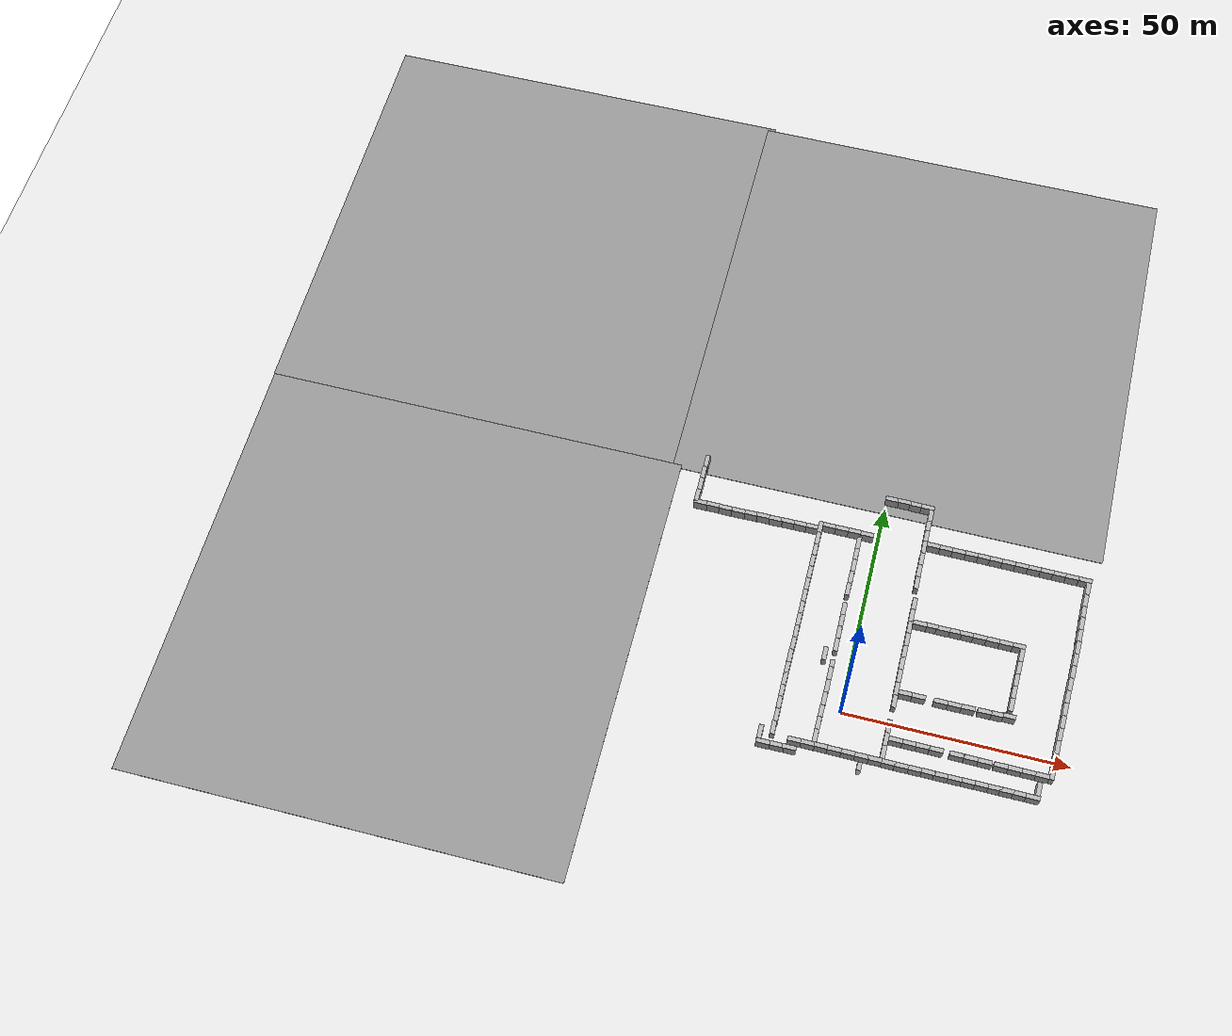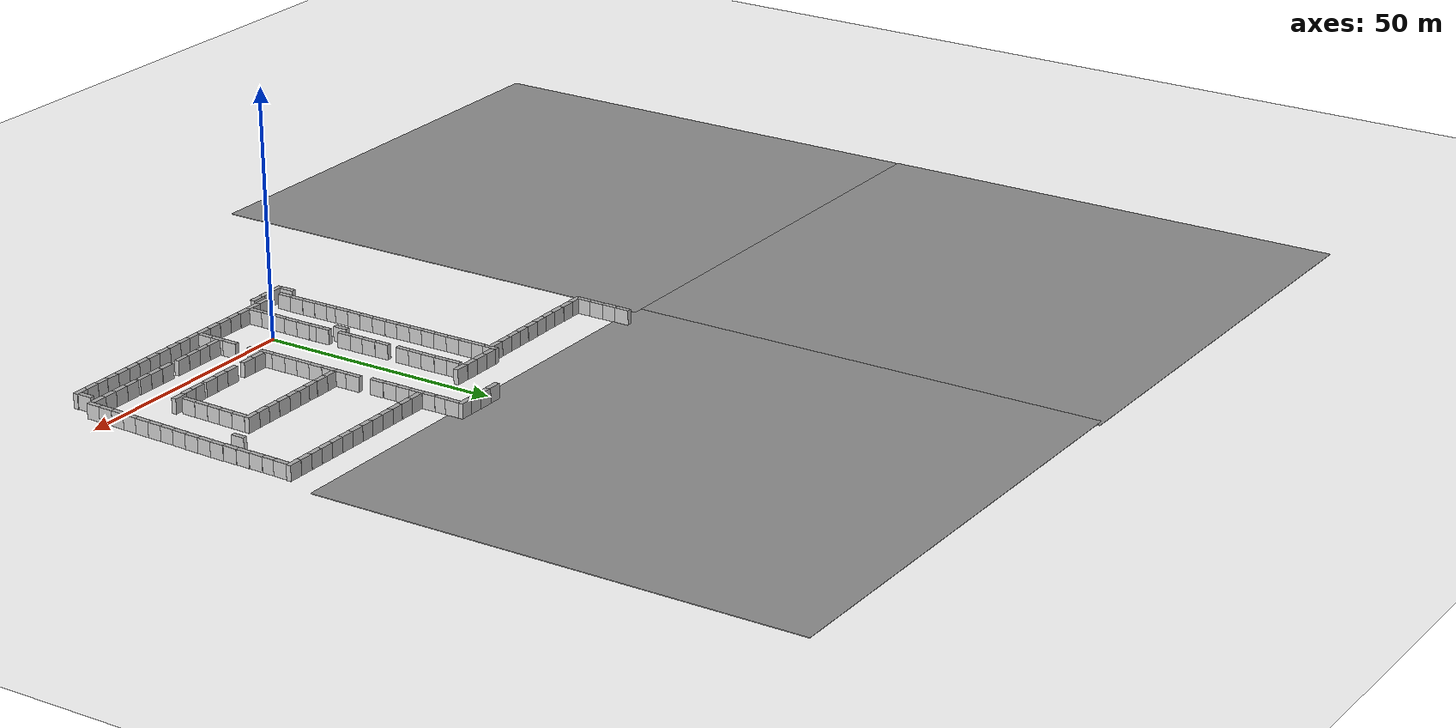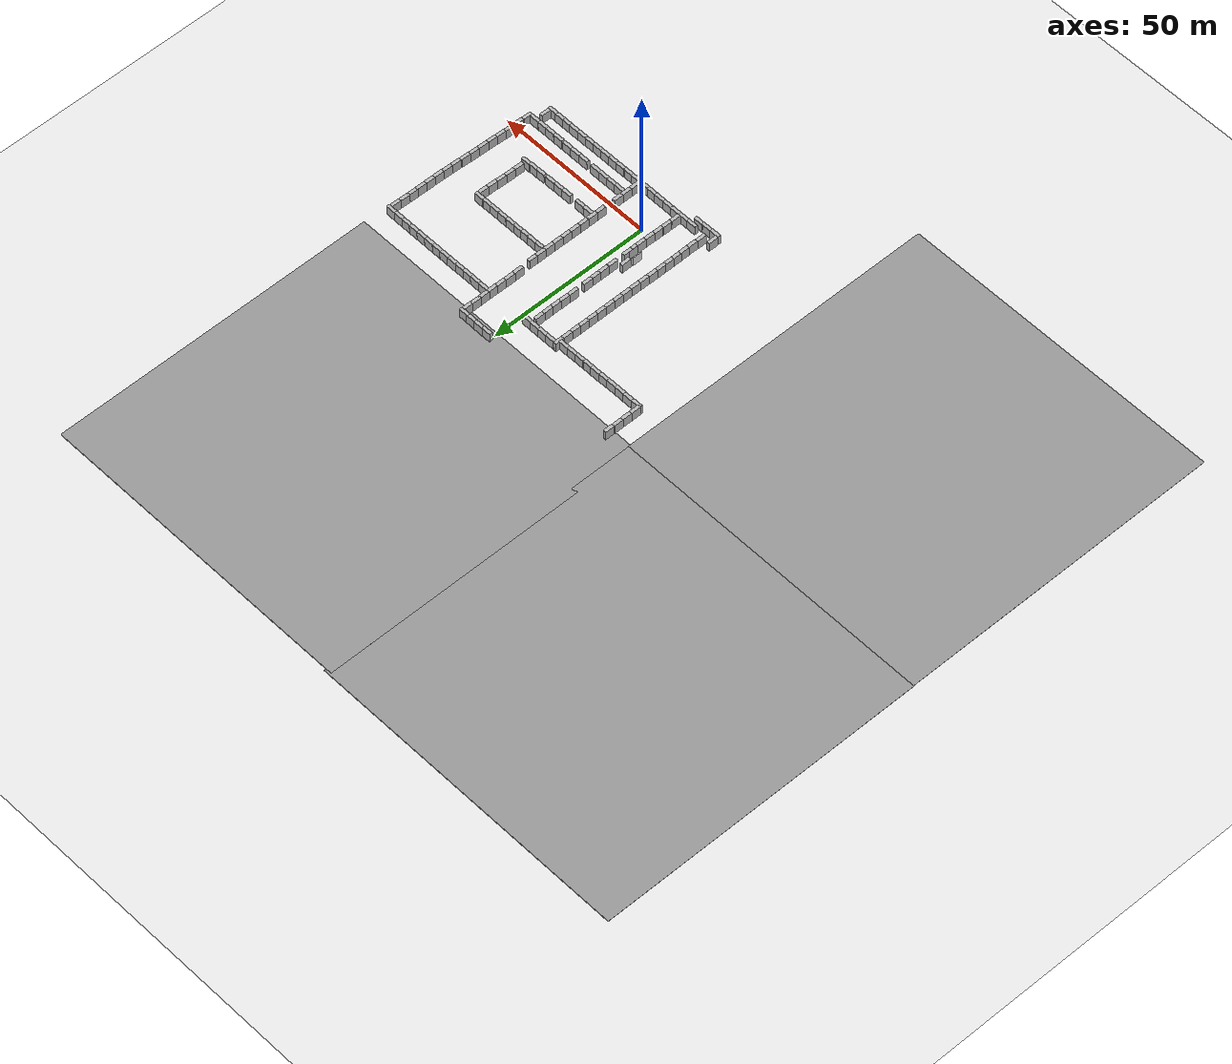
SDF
<sdf version="1.6">
 <world name="default">
  <light name="sun" type="directional">
   <pose>0 0 10 0 -0 0</pose>
   <diffuse>0.8 0.8 0.8 1</diffuse>
   <specular>0.2 0.2 0.2 1</specular>
   <attenuation>
    <range>1000</range>
    <constant>0.9</constant>
    <linear>0.01</linear>
    <quadratic>0.001</quadratic>
   </attenuation>
   <direction>-0.5 0.1 -0.9</direction>
  </light>
  <model name="ground_plane">
   <static>1</static>
   <link name="link">
    <collision name="collision">
     <geometry><plane><normal>0 0 1</normal><size>100 100</size></plane></geometry>
     <surface>
      <contact><collide_bitmask>65535</collide_bitmask></contact>
      <friction><ode><mu>100</mu><mu2>50</mu2></ode></friction>
     </surface>
    </collision>
    <visual name="visual">
     <cast_shadows>0</cast_shadows>
     <geometry><plane><normal>0 0 1</normal><size>100 100</size></plane></geometry>
     <material>
      <script><uri>file://media/materials/scripts/gazebo.material</uri><name>Gazebo/Grey</name></script>
     </material>
    </visual>
   </link>
  </model>
  <gravity>0 0 -9.8</gravity>
  <magnetic_field>6e-06 2.3e-05 -4.2e-05</magnetic_field>
  <atmosphere type="adiabatic"/>
  <physics name="default_physics" default="0" type="ode">
   <max_step_size>0.001</max_step_size>
   <real_time_factor>1</real_time_factor>
   <real_time_update_rate>1000</real_time_update_rate>
  </physics>
  <scene><ambient>0.4 0.4 0.4 1</ambient><background>0.7 0.7 0.7 1</background><shadows>1</shadows></scene>
  <audio><device>default</device></audio>
  <spherical_coordinates>
   <surface_model>EARTH_WGS84</surface_model>
   <latitude_deg>0</latitude_deg>
   <longitude_deg>0</longitude_deg>
   <elevation>0</elevation>
   <heading_deg>0</heading_deg>
  </spherical_coordinates>
  <model name="brick_box_3x1x3">
   <static>1</static>
   <link name="chassis">
    <pose>0 0 1.5 0 -0 0</pose>
    <collision name="collision"><geometry><box><size>3 1 3</size></box></geometry></collision>
    <visual name="visual">
     <geometry><mesh><uri>model://brick_box_3x1x3/meshes/simple_box.dae</uri><scale>3 1 3</scale></mesh></geometry>
     <material>
      <script>
       <uri>model://brick_box_3x1x3/materials/scripts</uri>
       <uri>model://brick_box_3x1x3/materials/textures</uri>
       <name>BrickBox/Diffuse</name>
      </script>
     </material>
    </visual>
   </link>
   <pose>-8.43725 -9.24492 0 0 -0 0</pose>
  </model>
  <model name="brick_box_3x1x3_clone">
   <static>1</static>
   <link name="chassis">
    <pose>0 0 1.5 0 -0 0</pose>
    <collision name="collision"><geometry><box><size>3 1 3</size></box></geometry></collision>
    <visual name="visual">
     <geometry><mesh><uri>model://brick_box_3x1x3/meshes/simple_box.dae</uri><scale>3 1 3</scale></mesh></geometry>
     <material>
      <script>
       <uri>model://brick_box_3x1x3/materials/scripts</uri>
       <uri>model://brick_box_3x1x3/materials/textures</uri>
       <name>BrickBox/Diffuse</name>
      </script>
     </material>
    </visual>
   </link>
   <pose>-5.50912 -9.21959 0 0 -0 0</pose>
  </model>
  <model name="brick_box_3x1x3_clone_0">
   <static>1</static>
   <link name="chassis">
    <pose>0 0 1.5 0 -0 0</pose>
    <collision name="collision"><geometry><box><size>3 1 3</size></box></geometry></collision>
    <visual name="visual">
     <geometry><mesh><uri>model://brick_box_3x1x3/meshes/simple_box.dae</uri><scale>3 1 3</scale></mesh></geometry>
     <material>
      <script>
       <uri>model://brick_box_3x1x3/materials/scripts</uri>
       <uri>model://brick_box_3x1x3/materials/textures</uri>
       <name>BrickBox/Diffuse</name>
      </script>
     </material>
    </visual>
   </link>
   <pose>-2.58798 -9.18934 0 0 -0 0</pose>
  </model>
  <model name="brick_box_3x1x3_clone_1">
   <static>1</static>
   <link name="chassis">
    <pose>0 0 1.5 0 -0 0</pose>
    <collision name="collision"><geometry><box><size>3 1 3</size></box></geometry></collision>
    <visual name="visual">
     <geometry><mesh><uri>model://brick_box_3x1x3/meshes/simple_box.dae</uri><scale>3 1 3</scale></mesh></geometry>
     <material>
      <script>
       <uri>model://brick_box_3x1x3/materials/scripts</uri>
       <uri>model://brick_box_3x1x3/materials/textures</uri>
       <name>BrickBox/Diffuse</name>
      </script>
     </material>
    </visual>
   </link>
   <pose>0.25233 -9.21535 0 0 -0 0</pose>
  </model>
  <model name="brick_box_3x1x3_clone_2">
   <static>1</static>
   <link name="chassis">
    <pose>0 0 1.5 0 -0 0</pose>
    <collision name="collision"><geometry><box><size>3 1 3</size></box></geometry></collision>
    <visual name="visual">
     <geometry><mesh><uri>model://brick_box_3x1x3/meshes/simple_box.dae</uri><scale>3 1 3</scale></mesh></geometry>
     <material>
      <script>
       <uri>model://brick_box_3x1x3/materials/scripts</uri>
       <uri>model://brick_box_3x1x3/materials/textures</uri>
       <name>BrickBox/Diffuse</name>
      </script>
     </material>
    </visual>
   </link>
   <pose>3.25958 -9.22941 0 0 -0 0</pose>
  </model>
  <model name="brick_box_3x1x3_clone_3">
   <static>1</static>
   <link name="chassis">
    <pose>0 0 1.5 0 -0 0</pose>
    <collision name="collision"><geometry><box><size>3 1 3</size></box></geometry></collision>
    <visual name="visual">
     <geometry><mesh><uri>model://brick_box_3x1x3/meshes/simple_box.dae</uri><scale>3 1 3</scale></mesh></geometry>
     <material>
      <script>
       <uri>model://brick_box_3x1x3/materials/scripts</uri>
       <uri>model://brick_box_3x1x3/materials/textures</uri>
       <name>BrickBox/Diffuse</name>
      </script>
     </material>
    </visual>
   </link>
   <pose>6.22517 -9.25435 0 0 -0 0</pose>
  </model>
  <model name="brick_box_3x1x3_clone_4">
   <static>1</static>
   <link name="chassis">
    <pose>0 0 1.5 0 -0 0</pose>
    <collision name="collision"><geometry><box><size>3 1 3</size></box></geometry></collision>
    <visual name="visual">
     <geometry><mesh><uri>model://brick_box_3x1x3/meshes/simple_box.dae</uri><scale>3 1 3</scale></mesh></geometry>
     <material>
      <script>
       <uri>model://brick_box_3x1x3/materials/scripts</uri>
       <uri>model://brick_box_3x1x3/materials/textures</uri>
       <name>BrickBox/Diffuse</name>
      </script>
     </material>
    </visual>
   </link>
   <pose>9.04758 -9.24556 0 0 -0 0</pose>
  </model>
  <model name="brick_box_3x1x3_clone_5">
   <static>1</static>
   <link name="chassis">
    <pose>0 0 1.5 0 -0 0</pose>
    <collision name="collision"><geometry><box><size>3 1 3</size></box></geometry></collision>
    <visual name="visual">
     <geometry><mesh><uri>model://brick_box_3x1x3/meshes/simple_box.dae</uri><scale>3 1 3</scale></mesh></geometry>
     <material>
      <script>
       <uri>model://brick_box_3x1x3/materials/scripts</uri>
       <uri>model://brick_box_3x1x3/materials/textures</uri>
       <name>BrickBox/Diffuse</name>
      </script>
     </material>
    </visual>
   </link>
   <pose>11.9991 -9.2785 0 0 -0 0</pose>
  </model>
  <model name="brick_box_3x1x3_clone_6">
   <static>1</static>
   <link name="chassis">
    <pose>0 0 1.5 0 -0 0</pose>
    <collision name="collision"><geometry><box><size>3 1 3</size></box></geometry></collision>
    <visual name="visual">
     <geometry><mesh><uri>model://brick_box_3x1x3/meshes/simple_box.dae</uri><scale>3 1 3</scale></mesh></geometry>
     <material>
      <script>
       <uri>model://brick_box_3x1x3/materials/scripts</uri>
       <uri>model://brick_box_3x1x3/materials/textures</uri>
       <name>BrickBox/Diffuse</name>
      </script>
     </material>
    </visual>
   </link>
   <pose>14.817 -9.29623 0 0 -0 0</pose>
  </model>
  <model name="brick_box_3x1x3_clone_7">
   <static>1</static>
   <link name="chassis">
    <pose>0 0 1.5 0 -0 0</pose>
    <collision name="collision"><geometry><box><size>3 1 3</size></box></geometry></collision>
    <visual name="visual">
     <geometry><mesh><uri>model://brick_box_3x1x3/meshes/simple_box.dae</uri><scale>3 1 3</scale></mesh></geometry>
     <material>
      <script>
       <uri>model://brick_box_3x1x3/materials/scripts</uri>
       <uri>model://brick_box_3x1x3/materials/textures</uri>
       <name>BrickBox/Diffuse</name>
      </script>
     </material>
    </visual>
   </link>
   <pose>17.5815 -9.27386 0 0 -0 0</pose>
  </model>
  <model name="brick_box_3x1x3_clone_8">
   <static>1</static>
   <link name="chassis">
    <pose>0 0 1.5 0 -0 0</pose>
    <collision name="collision"><geometry><box><size>3 1 3</size></box></geometry></collision>
    <visual name="visual">
     <geometry><mesh><uri>model://brick_box_3x1x3/meshes/simple_box.dae</uri><scale>3 1 3</scale></mesh></geometry>
     <material>
      <script>
       <uri>model://brick_box_3x1x3/materials/scripts</uri>
       <uri>model://brick_box_3x1x3/materials/textures</uri>
       <name>BrickBox/Diffuse</name>
      </script>
     </material>
    </visual>
   </link>
   <pose>20.5057 -9.24734 0 0 -0 0</pose>
  </model>
  <model name="brick_box_3x1x3_clone_9">
   <static>1</static>
   <link name="chassis">
    <pose>0 0 1.5 0 -0 0</pose>
    <collision name="collision"><geometry><box><size>3 1 3</size></box></geometry></collision>
    <visual name="visual">
     <geometry><mesh><uri>model://brick_box_3x1x3/meshes/simple_box.dae</uri><scale>3 1 3</scale></mesh></geometry>
     <material>
      <script>
       <uri>model://brick_box_3x1x3/materials/scripts</uri>
       <uri>model://brick_box_3x1x3/materials/textures</uri>
       <name>BrickBox/Diffuse</name>
      </script>
     </material>
    </visual>
   </link>
   <pose>23.2904 -9.26508 0 0 -0 0</pose>
  </model>
  <model name="brick_box_3x1x3_clone_10">
   <static>1</static>
   <link name="chassis">
    <pose>0 0 1.5 0 -0 0</pose>
    <collision name="collision"><geometry><box><size>3 1 3</size></box></geometry></collision>
    <visual name="visual">
     <geometry><mesh><uri>model://brick_box_3x1x3/meshes/simple_box.dae</uri><scale>3 1 3</scale></mesh></geometry>
     <material>
      <script>
       <uri>model://brick_box_3x1x3/materials/scripts</uri>
       <uri>model://brick_box_3x1x3/materials/textures</uri>
       <name>BrickBox/Diffuse</name>
      </script>
     </material>
    </visual>
   </link>
   <pose>26.1977 -9.25158 0 0 -0 0</pose>
  </model>
  <model name="brick_box_3x1x3_clone_11">
   <static>1</static>
   <link name="chassis">
    <pose>0 0 1.5 0 -0 0</pose>
    <collision name="collision"><geometry><box><size>3 1 3</size></box></geometry></collision>
    <visual name="visual">
     <geometry><mesh><uri>model://brick_box_3x1x3/meshes/simple_box.dae</uri><scale>3 1 3</scale></mesh></geometry>
     <material>
      <script>
       <uri>model://brick_box_3x1x3/materials/scripts</uri>
       <uri>model://brick_box_3x1x3/materials/textures</uri>
       <name>BrickBox/Diffuse</name>
      </script>
     </material>
    </visual>
   </link>
   <pose>29.084 -9.23354 0 0 -0 0</pose>
  </model>
  <model name="brick_box_3x1x3_clone_12">
   <static>1</static>
   <link name="chassis">
    <pose>0 0 1.5 0 -0 0</pose>
    <collision name="collision"><geometry><box><size>3 1 3</size></box></geometry></collision>
    <visual name="visual">
     <geometry><mesh><uri>model://brick_box_3x1x3/meshes/simple_box.dae</uri><scale>3 1 3</scale></mesh></geometry>
     <material>
      <script>
       <uri>model://brick_box_3x1x3/materials/scripts</uri>
       <uri>model://brick_box_3x1x3/materials/textures</uri>
       <name>BrickBox/Diffuse</name>
      </script>
     </material>
    </visual>
   </link>
   <pose>31.8711 -9.20709 0 0 -0 0</pose>
  </model>
  <model name="brick_box_3x1x3_0">
   <static>1</static>
   <link name="chassis">
    <pose>0 0 1.5 0 -0 0</pose>
    <collision name="collision"><geometry><box><size>3 1 3</size></box></geometry></collision>
    <visual name="visual">
     <geometry><mesh><uri>model://brick_box_3x1x3/meshes/simple_box.dae</uri><scale>3 1 3</scale></mesh></geometry>
     <material>
      <script>
       <uri>model://brick_box_3x1x3/materials/scripts</uri>
       <uri>model://brick_box_3x1x3/materials/textures</uri>
       <name>BrickBox/Diffuse</name>
      </script>
     </material>
    </visual>
   </link>
   <pose>6.6011 -4.08247 -21.1707 0 0 -1.56593</pose>
  </model>
  <model name="brick_box_3x1x3_1_clone">
   <static>1</static>
   <link name="chassis">
    <pose>0 0 1.5 0 -0 0</pose>
    <collision name="collision"><geometry><box><size>3 1 3</size></box></geometry></collision>
    <visual name="visual">
     <geometry><mesh><uri>model://brick_box_3x1x3/meshes/simple_box.dae</uri><scale>3 1 3</scale></mesh></geometry>
     <material>
      <script>
       <uri>model://brick_box_3x1x3/materials/scripts</uri>
       <uri>model://brick_box_3x1x3/materials/textures</uri>
       <name>BrickBox/Diffuse</name>
      </script>
     </material>
    </visual>
   </link>
   <pose>10.5266 -4.338 0 0 0 -1.56611</pose>
  </model>
  <model name="brick_box_3x1x3_1_clone_0">
   <static>1</static>
   <link name="chassis">
    <pose>0 0 1.5 0 -0 0</pose>
    <collision name="collision"><geometry><box><size>3 1 3</size></box></geometry></collision>
    <visual name="visual">
     <geometry><mesh><uri>model://brick_box_3x1x3/meshes/simple_box.dae</uri><scale>3 1 3</scale></mesh></geometry>
     <material>
      <script>
       <uri>model://brick_box_3x1x3/materials/scripts</uri>
       <uri>model://brick_box_3x1x3/materials/textures</uri>
       <name>BrickBox/Diffuse</name>
      </script>
     </material>
    </visual>
   </link>
   <pose>10.5341 -1.44104 0 0 0 -1.56611</pose>
  </model>
  <model name="brick_box_3x1x3_1_clone_1">
   <static>1</static>
   <link name="chassis">
    <pose>0 0 1.5 0 -0 0</pose>
    <collision name="collision"><geometry><box><size>3 1 3</size></box></geometry></collision>
    <visual name="visual">
     <geometry><mesh><uri>model://brick_box_3x1x3/meshes/simple_box.dae</uri><scale>3 1 3</scale></mesh></geometry>
     <material>
      <script>
       <uri>model://brick_box_3x1x3/materials/scripts</uri>
       <uri>model://brick_box_3x1x3/materials/textures</uri>
       <name>BrickBox/Diffuse</name>
      </script>
     </material>
    </visual>
   </link>
   <pose>10.6272 4.47727 0 0 0 -1.56611</pose>
  </model>
  <model name="brick_box_3x1x3_1_clone_2">
   <static>1</static>
   <link name="chassis">
    <pose>0 0 1.5 0 -0 0</pose>
    <collision name="collision"><geometry><box><size>3 1 3</size></box></geometry></collision>
    <visual name="visual">
     <geometry><mesh><uri>model://brick_box_3x1x3/meshes/simple_box.dae</uri><scale>3 1 3</scale></mesh></geometry>
     <material>
      <script>
       <uri>model://brick_box_3x1x3/materials/scripts</uri>
       <uri>model://brick_box_3x1x3/materials/textures</uri>
       <name>BrickBox/Diffuse</name>
      </script>
     </material>
    </visual>
   </link>
   <pose>10.576 7.33861 0 0 0 -1.56611</pose>
  </model>
  <model name="brick_box_3x1x3_1_clone_3">
   <static>1</static>
   <link name="chassis">
    <pose>0 0 1.5 0 -0 0</pose>
    <collision name="collision"><geometry><box><size>3 1 3</size></box></geometry></collision>
    <visual name="visual">
     <geometry><mesh><uri>model://brick_box_3x1x3/meshes/simple_box.dae</uri><scale>3 1 3</scale></mesh></geometry>
     <material>
      <script>
       <uri>model://brick_box_3x1x3/materials/scripts</uri>
       <uri>model://brick_box_3x1x3/materials/textures</uri>
       <name>BrickBox/Diffuse</name>
      </script>
     </material>
    </visual>
   </link>
   <pose>10.5928 10.3524 0 0 0 -1.56611</pose>
  </model>
  <model name="brick_box_3x1x3_1_clone_4">
   <static>1</static>
   <link name="chassis">
    <pose>0 0 1.5 0 -0 0</pose>
    <collision name="collision"><geometry><box><size>3 1 3</size></box></geometry></collision>
    <visual name="visual">
     <geometry><mesh><uri>model://brick_box_3x1x3/meshes/simple_box.dae</uri><scale>3 1 3</scale></mesh></geometry>
     <material>
      <script>
       <uri>model://brick_box_3x1x3/materials/scripts</uri>
       <uri>model://brick_box_3x1x3/materials/textures</uri>
       <name>BrickBox/Diffuse</name>
      </script>
     </material>
    </visual>
   </link>
   <pose>10.5723 13.2889 0 0 0 -1.56611</pose>
  </model>
  <model name="brick_box_3x1x3_1_clone_5">
   <static>1</static>
   <link name="chassis">
    <pose>0 0 1.5 0 -0 0</pose>
    <collision name="collision"><geometry><box><size>3 1 3</size></box></geometry></collision>
    <visual name="visual">
     <geometry><mesh><uri>model://brick_box_3x1x3/meshes/simple_box.dae</uri><scale>3 1 3</scale></mesh></geometry>
     <material>
      <script>
       <uri>model://brick_box_3x1x3/materials/scripts</uri>
       <uri>model://brick_box_3x1x3/materials/textures</uri>
       <name>BrickBox/Diffuse</name>
      </script>
     </material>
    </visual>
   </link>
   <pose>10.5988 16.1525 0 0 0 -1.56611</pose>
  </model>
  <model name="brick_box_3x1x3_1_clone_6">
   <static>1</static>
   <link name="chassis">
    <pose>0 0 1.5 0 -0 0</pose>
    <collision name="collision"><geometry><box><size>3 1 3</size></box></geometry></collision>
    <visual name="visual">
     <geometry><mesh><uri>model://brick_box_3x1x3/meshes/simple_box.dae</uri><scale>3 1 3</scale></mesh></geometry>
     <material>
      <script>
       <uri>model://brick_box_3x1x3/materials/scripts</uri>
       <uri>model://brick_box_3x1x3/materials/textures</uri>
       <name>BrickBox/Diffuse</name>
      </script>
     </material>
    </visual>
   </link>
   <pose>10.6319 19.0549 0 0 0 -1.56611</pose>
  </model>
  <model name="brick_box_3x1x3_1_clone_7">
   <static>1</static>
   <link name="chassis">
    <pose>0 0 1.5 0 -0 0</pose>
    <collision name="collision"><geometry><box><size>3 1 3</size></box></geometry></collision>
    <visual name="visual">
     <geometry><mesh><uri>model://brick_box_3x1x3/meshes/simple_box.dae</uri><scale>3 1 3</scale></mesh></geometry>
     <material>
      <script>
       <uri>model://brick_box_3x1x3/materials/scripts</uri>
       <uri>model://brick_box_3x1x3/materials/textures</uri>
       <name>BrickBox/Diffuse</name>
      </script>
     </material>
    </visual>
   </link>
   <pose>10.6106 21.95 0 0 0 -1.56611</pose>
  </model>
  <model name="brick_box_3x1x3_1_clone_8">
   <static>1</static>
   <link name="chassis">
    <pose>0 0 1.5 0 -0 0</pose>
    <collision name="collision"><geometry><box><size>3 1 3</size></box></geometry></collision>
    <visual name="visual">
     <geometry><mesh><uri>model://brick_box_3x1x3/meshes/simple_box.dae</uri><scale>3 1 3</scale></mesh></geometry>
     <material>
      <script>
       <uri>model://brick_box_3x1x3/materials/scripts</uri>
       <uri>model://brick_box_3x1x3/materials/textures</uri>
       <name>BrickBox/Diffuse</name>
      </script>
     </material>
    </visual>
   </link>
   <pose>10.5896 24.8323 0 0 0 -1.56611</pose>
  </model>
  <model name="brick_box_3x1x3_1_clone_9">
   <static>1</static>
   <link name="chassis">
    <pose>0 0 1.5 0 -0 0</pose>
    <collision name="collision"><geometry><box><size>3 1 3</size></box></geometry></collision>
    <visual name="visual">
     <geometry><mesh><uri>model://brick_box_3x1x3/meshes/simple_box.dae</uri><scale>3 1 3</scale></mesh></geometry>
     <material>
      <script>
       <uri>model://brick_box_3x1x3/materials/scripts</uri>
       <uri>model://brick_box_3x1x3/materials/textures</uri>
       <name>BrickBox/Diffuse</name>
      </script>
     </material>
    </visual>
   </link>
   <pose>10.6094 27.593 0 0 0 -1.56611</pose>
  </model>
  <model name="brick_box_3x1x3_2">
   <static>1</static>
   <link name="chassis">
    <pose>0 0 1.5 0 -0 0</pose>
    <collision name="collision"><geometry><box><size>3 1 3</size></box></geometry></collision>
    <visual name="visual">
     <geometry><mesh><uri>model://brick_box_3x1x3/meshes/simple_box.dae</uri><scale>3 1 3</scale></mesh></geometry>
     <material>
      <script>
       <uri>model://brick_box_3x1x3/materials/scripts</uri>
       <uri>model://brick_box_3x1x3/materials/textures</uri>
       <name>BrickBox/Diffuse</name>
      </script>
     </material>
    </visual>
   </link>
   <pose>12.5701 6.74415 0 0 -0 0</pose>
  </model>
  <model name="brick_box_3x1x3_2_clone">
   <static>1</static>
   <link name="chassis">
    <pose>0 0 1.5 0 -0 0</pose>
    <collision name="collision"><geometry><box><size>3 1 3</size></box></geometry></collision>
    <visual name="visual">
     <geometry><mesh><uri>model://brick_box_3x1x3/meshes/simple_box.dae</uri><scale>3 1 3</scale></mesh></geometry>
     <material>
      <script>
       <uri>model://brick_box_3x1x3/materials/scripts</uri>
       <uri>model://brick_box_3x1x3/materials/textures</uri>
       <name>BrickBox/Diffuse</name>
      </script>
     </material>
    </visual>
   </link>
   <pose>15.5163 6.75439 0 0 -0 0</pose>
  </model>
  <model name="brick_box_3x1x3_1_clone_clone">
   <static>1</static>
   <link name="chassis">
    <pose>0 0 1.5 0 -0 0</pose>
    <collision name="collision"><geometry><box><size>3 1 3</size></box></geometry></collision>
    <visual name="visual">
     <geometry><mesh><uri>model://brick_box_3x1x3/meshes/simple_box.dae</uri><scale>3 1 3</scale></mesh></geometry>
     <material>
      <script>
       <uri>model://brick_box_3x1x3/materials/scripts</uri>
       <uri>model://brick_box_3x1x3/materials/textures</uri>
       <name>BrickBox/Diffuse</name>
      </script>
     </material>
    </visual>
   </link>
   <pose>10.5129 -7.30151 0 0 0 -1.56611</pose>
  </model>
  <model name="brick_box_3x1x3_2_clone_clone">
   <static>1</static>
   <link name="chassis">
    <pose>0 0 1.5 0 -0 0</pose>
    <collision name="collision"><geometry><box><size>3 1 3</size></box></geometry></collision>
    <visual name="visual">
     <geometry><mesh><uri>model://brick_box_3x1x3/meshes/simple_box.dae</uri><scale>3 1 3</scale></mesh></geometry>
     <material>
      <script>
       <uri>model://brick_box_3x1x3/materials/scripts</uri>
       <uri>model://brick_box_3x1x3/materials/textures</uri>
       <name>BrickBox/Diffuse</name>
      </script>
     </material>
    </visual>
   </link>
   <pose>20.3482 6.7602 0 0 -0 0</pose>
  </model>
  <model name="brick_box_3x1x3_2_clone_clone_0">
   <static>1</static>
   <link name="chassis">
    <pose>0 0 1.5 0 -0 0</pose>
    <collision name="collision"><geometry><box><size>3 1 3</size></box></geometry></collision>
    <visual name="visual">
     <geometry><mesh><uri>model://brick_box_3x1x3/meshes/simple_box.dae</uri><scale>3 1 3</scale></mesh></geometry>
     <material>
      <script>
       <uri>model://brick_box_3x1x3/materials/scripts</uri>
       <uri>model://brick_box_3x1x3/materials/textures</uri>
       <name>BrickBox/Diffuse</name>
      </script>
     </material>
    </visual>
   </link>
   <pose>12.7018 23.419 0 0 -0 0</pose>
  </model>
  <model name="brick_box_3x1x3_2_clone_clone_1">
   <static>1</static>
   <link name="chassis">
    <pose>0 0 1.5 0 -0 0</pose>
    <collision name="collision"><geometry><box><size>3 1 3</size></box></geometry></collision>
    <visual name="visual">
     <geometry><mesh><uri>model://brick_box_3x1x3/meshes/simple_box.dae</uri><scale>3 1 3</scale></mesh></geometry>
     <material>
      <script>
       <uri>model://brick_box_3x1x3/materials/scripts</uri>
       <uri>model://brick_box_3x1x3/materials/textures</uri>
       <name>BrickBox/Diffuse</name>
      </script>
     </material>
    </visual>
   </link>
   <pose>15.2225 23.4641 0 0 -0 0</pose>
  </model>
  <model name="brick_box_3x1x3_2_clone_clone_2">
   <static>1</static>
   <link name="chassis">
    <pose>0 0 1.5 0 -0 0</pose>
    <collision name="collision"><geometry><box><size>3 1 3</size></box></geometry></collision>
    <visual name="visual">
     <geometry><mesh><uri>model://brick_box_3x1x3/meshes/simple_box.dae</uri><scale>3 1 3</scale></mesh></geometry>
     <material>
      <script>
       <uri>model://brick_box_3x1x3/materials/scripts</uri>
       <uri>model://brick_box_3x1x3/materials/textures</uri>
       <name>BrickBox/Diffuse</name>
      </script>
     </material>
    </visual>
   </link>
   <pose>17.8816 23.4199 0 0 -0 0</pose>
  </model>
  <model name="brick_box_3x1x3_2_clone_clone_3">
   <static>1</static>
   <link name="chassis">
    <pose>0 0 1.5 0 -0 0</pose>
    <collision name="collision"><geometry><box><size>3 1 3</size></box></geometry></collision>
    <visual name="visual">
     <geometry><mesh><uri>model://brick_box_3x1x3/meshes/simple_box.dae</uri><scale>3 1 3</scale></mesh></geometry>
     <material>
      <script>
       <uri>model://brick_box_3x1x3/materials/scripts</uri>
       <uri>model://brick_box_3x1x3/materials/textures</uri>
       <name>BrickBox/Diffuse</name>
      </script>
     </material>
    </visual>
   </link>
   <pose>20.5136 23.4661 0 0 -0 0</pose>
  </model>
  <model name="brick_box_3x1x3_2_clone_clone_4">
   <static>1</static>
   <link name="chassis">
    <pose>0 0 1.5 0 -0 0</pose>
    <collision name="collision"><geometry><box><size>3 1 3</size></box></geometry></collision>
    <visual name="visual">
     <geometry><mesh><uri>model://brick_box_3x1x3/meshes/simple_box.dae</uri><scale>3 1 3</scale></mesh></geometry>
     <material>
      <script>
       <uri>model://brick_box_3x1x3/materials/scripts</uri>
       <uri>model://brick_box_3x1x3/materials/textures</uri>
       <name>BrickBox/Diffuse</name>
      </script>
     </material>
    </visual>
   </link>
   <pose>23.0714 23.4688 0 0 -0 0</pose>
  </model>
  <model name="brick_box_3x1x3_2_clone_clone_5">
   <static>1</static>
   <link name="chassis">
    <pose>0 0 1.5 0 -0 0</pose>
    <collision name="collision"><geometry><box><size>3 1 3</size></box></geometry></collision>
    <visual name="visual">
     <geometry><mesh><uri>model://brick_box_3x1x3/meshes/simple_box.dae</uri><scale>3 1 3</scale></mesh></geometry>
     <material>
      <script>
       <uri>model://brick_box_3x1x3/materials/scripts</uri>
       <uri>model://brick_box_3x1x3/materials/textures</uri>
       <name>BrickBox/Diffuse</name>
      </script>
     </material>
    </visual>
   </link>
   <pose>26.0277 23.485 0 0 -0 0</pose>
  </model>
  <model name="brick_box_3x1x3_2_clone_clone_6">
   <static>1</static>
   <link name="chassis">
    <pose>0 0 1.5 0 -0 0</pose>
    <collision name="collision"><geometry><box><size>3 1 3</size></box></geometry></collision>
    <visual name="visual">
     <geometry><mesh><uri>model://brick_box_3x1x3/meshes/simple_box.dae</uri><scale>3 1 3</scale></mesh></geometry>
     <material>
      <script>
       <uri>model://brick_box_3x1x3/materials/scripts</uri>
       <uri>model://brick_box_3x1x3/materials/textures</uri>
       <name>BrickBox/Diffuse</name>
      </script>
     </material>
    </visual>
   </link>
   <pose>23.3403 6.79053 -0 0 -0 0</pose>
  </model>
  <model name="brick_box_3x1x3_2_clone_clone_7">
   <static>1</static>
   <link name="chassis">
    <pose>0 0 1.5 0 -0 0</pose>
    <collision name="collision"><geometry><box><size>3 1 3</size></box></geometry></collision>
    <visual name="visual">
     <geometry><mesh><uri>model://brick_box_3x1x3/meshes/simple_box.dae</uri><scale>3 1 3</scale></mesh></geometry>
     <material>
      <script>
       <uri>model://brick_box_3x1x3/materials/scripts</uri>
       <uri>model://brick_box_3x1x3/materials/textures</uri>
       <name>BrickBox/Diffuse</name>
      </script>
     </material>
    </visual>
   </link>
   <pose>26.3145 6.82745 0 0 -0 0</pose>
  </model>
  <model name="brick_box_3x1x3_2_clone_clone_8">
   <static>1</static>
   <link name="chassis">
    <pose>0 0 1.5 0 -0 0</pose>
    <collision name="collision"><geometry><box><size>3 1 3</size></box></geometry></collision>
    <visual name="visual">
     <geometry><mesh><uri>model://brick_box_3x1x3/meshes/simple_box.dae</uri><scale>3 1 3</scale></mesh></geometry>
     <material>
      <script>
       <uri>model://brick_box_3x1x3/materials/scripts</uri>
       <uri>model://brick_box_3x1x3/materials/textures</uri>
       <name>BrickBox/Diffuse</name>
      </script>
     </material>
    </visual>
   </link>
   <pose>12.5628 -4.01157 0 0 -0 0</pose>
  </model>
  <model name="brick_box_3x1x3_2_clone_clone_9">
   <static>1</static>
   <link name="chassis">
    <pose>0 0 1.5 0 -0 0</pose>
    <collision name="collision"><geometry><box><size>3 1 3</size></box></geometry></collision>
    <visual name="visual">
     <geometry><mesh><uri>model://brick_box_3x1x3/meshes/simple_box.dae</uri><scale>3 1 3</scale></mesh></geometry>
     <material>
      <script>
       <uri>model://brick_box_3x1x3/materials/scripts</uri>
       <uri>model://brick_box_3x1x3/materials/textures</uri>
       <name>BrickBox/Diffuse</name>
      </script>
     </material>
    </visual>
   </link>
   <pose>15.533 -4.01271 0 0 -0 0</pose>
  </model>
  <model name="brick_box_3x1x3_2_clone_clone_10">
   <static>1</static>
   <link name="chassis">
    <pose>0 0 1.5 0 -0 0</pose>
    <collision name="collision"><geometry><box><size>3 1 3</size></box></geometry></collision>
    <visual name="visual">
     <geometry><mesh><uri>model://brick_box_3x1x3/meshes/simple_box.dae</uri><scale>3 1 3</scale></mesh></geometry>
     <material>
      <script>
       <uri>model://brick_box_3x1x3/materials/scripts</uri>
       <uri>model://brick_box_3x1x3/materials/textures</uri>
       <name>BrickBox/Diffuse</name>
      </script>
     </material>
    </visual>
   </link>
   <pose>18.3198 -4.00332 0 0 -0 0</pose>
  </model>
  <model name="brick_box_3x1x3_2_clone_clone_11">
   <static>1</static>
   <link name="chassis">
    <pose>0 0 1.5 0 -0 0</pose>
    <collision name="collision"><geometry><box><size>3 1 3</size></box></geometry></collision>
    <visual name="visual">
     <geometry><mesh><uri>model://brick_box_3x1x3/meshes/simple_box.dae</uri><scale>3 1 3</scale></mesh></geometry>
     <material>
      <script>
       <uri>model://brick_box_3x1x3/materials/scripts</uri>
       <uri>model://brick_box_3x1x3/materials/textures</uri>
       <name>BrickBox/Diffuse</name>
      </script>
     </material>
    </visual>
   </link>
   <pose>21.3436 -4.01413 0 0 -0 0</pose>
  </model>
  <model name="brick_box_3x1x3_2_clone_clone_12">
   <static>1</static>
   <link name="chassis">
    <pose>0 0 1.5 0 -0 0</pose>
    <collision name="collision"><geometry><box><size>3 1 3</size></box></geometry></collision>
    <visual name="visual">
     <geometry><mesh><uri>model://brick_box_3x1x3/meshes/simple_box.dae</uri><scale>3 1 3</scale></mesh></geometry>
     <material>
      <script>
       <uri>model://brick_box_3x1x3/materials/scripts</uri>
       <uri>model://brick_box_3x1x3/materials/textures</uri>
       <name>BrickBox/Diffuse</name>
      </script>
     </material>
    </visual>
   </link>
   <pose>25.7322 -4.03221 0 0 -0 0</pose>
  </model>
  <model name="brick_box_3x1x3_2_clone_clone_13">
   <static>1</static>
   <link name="chassis">
    <pose>0 0 1.5 0 -0 0</pose>
    <collision name="collision"><geometry><box><size>3 1 3</size></box></geometry></collision>
    <visual name="visual">
     <geometry><mesh><uri>model://brick_box_3x1x3/meshes/simple_box.dae</uri><scale>3 1 3</scale></mesh></geometry>
     <material>
      <script>
       <uri>model://brick_box_3x1x3/materials/scripts</uri>
       <uri>model://brick_box_3x1x3/materials/textures</uri>
       <name>BrickBox/Diffuse</name>
      </script>
     </material>
    </visual>
   </link>
   <pose>28.8146 -4.05727 0 0 -0 0</pose>
  </model>
  <model name="brick_box_3x1x3_2_clone_clone_14">
   <static>1</static>
   <link name="chassis">
    <pose>0 0 1.5 0 -0 0</pose>
    <collision name="collision"><geometry><box><size>3 1 3</size></box></geometry></collision>
    <visual name="visual">
     <geometry><mesh><uri>model://brick_box_3x1x3/meshes/simple_box.dae</uri><scale>3 1 3</scale></mesh></geometry>
     <material>
      <script>
       <uri>model://brick_box_3x1x3/materials/scripts</uri>
       <uri>model://brick_box_3x1x3/materials/textures</uri>
       <name>BrickBox/Diffuse</name>
      </script>
     </material>
    </visual>
   </link>
   <pose>31.8039 -4.08645 0 0 -0 0</pose>
  </model>
  <model name="brick_box_3x1x3_2_clone_clone_15">
   <static>1</static>
   <link name="chassis">
    <pose>0 0 1.5 0 -0 0</pose>
    <collision name="collision"><geometry><box><size>3 1 3</size></box></geometry></collision>
    <visual name="visual">
     <geometry><mesh><uri>model://brick_box_3x1x3/meshes/simple_box.dae</uri><scale>3 1 3</scale></mesh></geometry>
     <material>
      <script>
       <uri>model://brick_box_3x1x3/materials/scripts</uri>
       <uri>model://brick_box_3x1x3/materials/textures</uri>
       <name>BrickBox/Diffuse</name>
      </script>
     </material>
    </visual>
   </link>
   <pose>35.2557 -4.10464 0 0 -0 0</pose>
  </model>
  <model name="brick_box_3x1x3_2_clone_clone_16">
   <static>1</static>
   <link name="chassis">
    <pose>0 0 1.5 0 -0 0</pose>
    <collision name="collision"><geometry><box><size>3 1 3</size></box></geometry></collision>
    <visual name="visual">
     <geometry><mesh><uri>model://brick_box_3x1x3/meshes/simple_box.dae</uri><scale>3 1 3</scale></mesh></geometry>
     <material>
      <script>
       <uri>model://brick_box_3x1x3/materials/scripts</uri>
       <uri>model://brick_box_3x1x3/materials/textures</uri>
       <name>BrickBox/Diffuse</name>
      </script>
     </material>
    </visual>
   </link>
   <pose>38.2081 -4.12264 0 0 -0 0</pose>
  </model>
  <model name="brick_box_3x1x3_2_clone_clone_17">
   <static>1</static>
   <link name="chassis">
    <pose>0 0 1.5 0 -0 0</pose>
    <collision name="collision"><geometry><box><size>3 1 3</size></box></geometry></collision>
    <visual name="visual">
     <geometry><mesh><uri>model://brick_box_3x1x3/meshes/simple_box.dae</uri><scale>3 1 3</scale></mesh></geometry>
     <material>
      <script>
       <uri>model://brick_box_3x1x3/materials/scripts</uri>
       <uri>model://brick_box_3x1x3/materials/textures</uri>
       <name>BrickBox/Diffuse</name>
      </script>
     </material>
    </visual>
   </link>
   <pose>41.1147 -4.13236 0 0 -0 0</pose>
  </model>
  <model name="brick_box_3x1x3_2_clone_clone_18">
   <static>1</static>
   <link name="chassis">
    <pose>0 0 1.5 0 -0 0</pose>
    <collision name="collision"><geometry><box><size>3 1 3</size></box></geometry></collision>
    <visual name="visual">
     <geometry><mesh><uri>model://brick_box_3x1x3/meshes/simple_box.dae</uri><scale>3 1 3</scale></mesh></geometry>
     <material>
      <script>
       <uri>model://brick_box_3x1x3/materials/scripts</uri>
       <uri>model://brick_box_3x1x3/materials/textures</uri>
       <name>BrickBox/Diffuse</name>
      </script>
     </material>
    </visual>
   </link>
   <pose>44.0173 -4.125 0 0 -0 0</pose>
  </model>
  <model name="brick_box_3x1x3_2_clone_clone_19">
   <static>1</static>
   <link name="chassis">
    <pose>0 0 1.5 0 -0 0</pose>
    <collision name="collision"><geometry><box><size>3 1 3</size></box></geometry></collision>
    <visual name="visual">
     <geometry><mesh><uri>model://brick_box_3x1x3/meshes/simple_box.dae</uri><scale>3 1 3</scale></mesh></geometry>
     <material>
      <script>
       <uri>model://brick_box_3x1x3/materials/scripts</uri>
       <uri>model://brick_box_3x1x3/materials/textures</uri>
       <name>BrickBox/Diffuse</name>
      </script>
     </material>
    </visual>
   </link>
   <pose>29.8885 6.88605 0 0 -0 0</pose>
  </model>
  <model name="brick_box_3x1x3_2_clone_clone_20">
   <static>1</static>
   <link name="chassis">
    <pose>0 0 1.5 0 -0 0</pose>
    <collision name="collision"><geometry><box><size>3 1 3</size></box></geometry></collision>
    <visual name="visual">
     <geometry><mesh><uri>model://brick_box_3x1x3/meshes/simple_box.dae</uri><scale>3 1 3</scale></mesh></geometry>
     <material>
      <script>
       <uri>model://brick_box_3x1x3/materials/scripts</uri>
       <uri>model://brick_box_3x1x3/materials/textures</uri>
       <name>BrickBox/Diffuse</name>
      </script>
     </material>
    </visual>
   </link>
   <pose>32.4248 6.94027 0 0 -0 0</pose>
  </model>
  <model name="brick_box_3x1x3_2_clone_clone_21">
   <static>1</static>
   <link name="chassis">
    <pose>0 0 1.5 0 -0 0</pose>
    <collision name="collision"><geometry><box><size>3 1 3</size></box></geometry></collision>
    <visual name="visual">
     <geometry><mesh><uri>model://brick_box_3x1x3/meshes/simple_box.dae</uri><scale>3 1 3</scale></mesh></geometry>
     <material>
      <script>
       <uri>model://brick_box_3x1x3/materials/scripts</uri>
       <uri>model://brick_box_3x1x3/materials/textures</uri>
       <name>BrickBox/Diffuse</name>
      </script>
     </material>
    </visual>
   </link>
   <pose>35.0781 7.09899 0 0 -0 0</pose>
  </model>
  <model name="brick_box_3x1x3_2_clone_clone_22">
   <static>1</static>
   <link name="chassis">
    <pose>0 0 1.5 0 -0 0</pose>
    <collision name="collision"><geometry><box><size>3 1 3</size></box></geometry></collision>
    <visual name="visual">
     <geometry><mesh><uri>model://brick_box_3x1x3/meshes/simple_box.dae</uri><scale>3 1 3</scale></mesh></geometry>
     <material>
      <script>
       <uri>model://brick_box_3x1x3/materials/scripts</uri>
       <uri>model://brick_box_3x1x3/materials/textures</uri>
       <name>BrickBox/Diffuse</name>
      </script>
     </material>
    </visual>
   </link>
   <pose>28.8854 23.4647 0 0 -0 0</pose>
  </model>
  <model name="brick_box_3x1x3_2_clone_clone_23">
   <static>1</static>
   <link name="chassis">
    <pose>0 0 1.5 0 -0 0</pose>
    <collision name="collision"><geometry><box><size>3 1 3</size></box></geometry></collision>
    <visual name="visual">
     <geometry><mesh><uri>model://brick_box_3x1x3/meshes/simple_box.dae</uri><scale>3 1 3</scale></mesh></geometry>
     <material>
      <script>
       <uri>model://brick_box_3x1x3/materials/scripts</uri>
       <uri>model://brick_box_3x1x3/materials/textures</uri>
       <name>BrickBox/Diffuse</name>
      </script>
     </material>
    </visual>
   </link>
   <pose>31.8378 23.4712 0 0 -0 0</pose>
  </model>
  <model name="brick_box_3x1x3_2_clone_clone_24">
   <static>1</static>
   <link name="chassis">
    <pose>0 0 1.5 0 -0 0</pose>
    <collision name="collision"><geometry><box><size>3 1 3</size></box></geometry></collision>
    <visual name="visual">
     <geometry><mesh><uri>model://brick_box_3x1x3/meshes/simple_box.dae</uri><scale>3 1 3</scale></mesh></geometry>
     <material>
      <script>
       <uri>model://brick_box_3x1x3/materials/scripts</uri>
       <uri>model://brick_box_3x1x3/materials/textures</uri>
       <name>BrickBox/Diffuse</name>
      </script>
     </material>
    </visual>
   </link>
   <pose>34.5713 23.5159 0 0 -0 0</pose>
  </model>
  <model name="brick_box_3x1x3_1">
   <static>1</static>
   <link name="chassis">
    <pose>0 0 1.5 0 -0 0</pose>
    <collision name="collision"><geometry><box><size>3 1 3</size></box></geometry></collision>
    <visual name="visual">
     <geometry><mesh><uri>model://brick_box_3x1x3/meshes/simple_box.dae</uri><scale>3 1 3</scale></mesh></geometry>
     <material>
      <script>
       <uri>model://brick_box_3x1x3/materials/scripts</uri>
       <uri>model://brick_box_3x1x3/materials/textures</uri>
       <name>BrickBox/Diffuse</name>
      </script>
     </material>
    </visual>
   </link>
   <pose>35.542 21.5109 0 0 0 -1.59732</pose>
  </model>
  <model name="brick_box_3x1x3_1_clone_10">
   <static>1</static>
   <link name="chassis">
    <pose>0 0 1.5 0 -0 0</pose>
    <collision name="collision"><geometry><box><size>3 1 3</size></box></geometry></collision>
    <visual name="visual">
     <geometry><mesh><uri>model://brick_box_3x1x3/meshes/simple_box.dae</uri><scale>3 1 3</scale></mesh></geometry>
     <material>
      <script>
       <uri>model://brick_box_3x1x3/materials/scripts</uri>
       <uri>model://brick_box_3x1x3/materials/textures</uri>
       <name>BrickBox/Diffuse</name>
      </script>
     </material>
    </visual>
   </link>
   <pose>35.4702 18.5428 0 0 0 -1.59732</pose>
  </model>
  <model name="brick_box_3x1x3_1_clone_11">
   <static>1</static>
   <link name="chassis">
    <pose>0 0 1.5 0 -0 0</pose>
    <collision name="collision"><geometry><box><size>3 1 3</size></box></geometry></collision>
    <visual name="visual">
     <geometry><mesh><uri>model://brick_box_3x1x3/meshes/simple_box.dae</uri><scale>3 1 3</scale></mesh></geometry>
     <material>
      <script>
       <uri>model://brick_box_3x1x3/materials/scripts</uri>
       <uri>model://brick_box_3x1x3/materials/textures</uri>
       <name>BrickBox/Diffuse</name>
      </script>
     </material>
    </visual>
   </link>
   <pose>35.3544 15.6428 0 0 0 -1.59732</pose>
  </model>
  <model name="brick_box_3x1x3_1_clone_12">
   <static>1</static>
   <link name="chassis">
    <pose>0 0 1.5 0 -0 0</pose>
    <collision name="collision"><geometry><box><size>3 1 3</size></box></geometry></collision>
    <visual name="visual">
     <geometry><mesh><uri>model://brick_box_3x1x3/meshes/simple_box.dae</uri><scale>3 1 3</scale></mesh></geometry>
     <material>
      <script>
       <uri>model://brick_box_3x1x3/materials/scripts</uri>
       <uri>model://brick_box_3x1x3/materials/textures</uri>
       <name>BrickBox/Diffuse</name>
      </script>
     </material>
    </visual>
   </link>
   <pose>35.2916 12.7432 0 0 0 -1.59732</pose>
  </model>
  <model name="brick_box_3x1x3_1_clone_13">
   <static>1</static>
   <link name="chassis">
    <pose>0 0 1.5 0 -0 0</pose>
    <collision name="collision"><geometry><box><size>3 1 3</size></box></geometry></collision>
    <visual name="visual">
     <geometry><mesh><uri>model://brick_box_3x1x3/meshes/simple_box.dae</uri><scale>3 1 3</scale></mesh></geometry>
     <material>
      <script>
       <uri>model://brick_box_3x1x3/materials/scripts</uri>
       <uri>model://brick_box_3x1x3/materials/textures</uri>
       <name>BrickBox/Diffuse</name>
      </script>
     </material>
    </visual>
   </link>
   <pose>35.2291 9.79115 0 0 0 -1.59732</pose>
  </model>
  <model name="brick_box_3x1x3_clone_12_clone">
   <static>1</static>
   <link name="chassis">
    <pose>0 0 1.5 0 -0 0</pose>
    <collision name="collision"><geometry><box><size>3 1 3</size></box></geometry></collision>
    <visual name="visual">
     <geometry><mesh><uri>model://brick_box_3x1x3/meshes/simple_box.dae</uri><scale>3 1 3</scale></mesh></geometry>
     <material>
      <script>
       <uri>model://brick_box_3x1x3/materials/scripts</uri>
       <uri>model://brick_box_3x1x3/materials/textures</uri>
       <name>BrickBox/Diffuse</name>
      </script>
     </material>
    </visual>
   </link>
   <pose>34.84 -9.20404 0 0 -0 0</pose>
  </model>
  <model name="brick_box_3x1x3_clone_12_clone_0">
   <static>1</static>
   <link name="chassis">
    <pose>0 0 1.5 0 -0 0</pose>
    <collision name="collision"><geometry><box><size>3 1 3</size></box></geometry></collision>
    <visual name="visual">
     <geometry><mesh><uri>model://brick_box_3x1x3/meshes/simple_box.dae</uri><scale>3 1 3</scale></mesh></geometry>
     <material>
      <script>
       <uri>model://brick_box_3x1x3/materials/scripts</uri>
       <uri>model://brick_box_3x1x3/materials/textures</uri>
       <name>BrickBox/Diffuse</name>
      </script>
     </material>
    </visual>
   </link>
   <pose>37.3458 -9.21914 0 0 -0 0</pose>
  </model>
  <model name="brick_box_3x1x3_clone_12_clone_1">
   <static>1</static>
   <link name="chassis">
    <pose>0 0 1.5 0 -0 0</pose>
    <collision name="collision"><geometry><box><size>3 1 3</size></box></geometry></collision>
    <visual name="visual">
     <geometry><mesh><uri>model://brick_box_3x1x3/meshes/simple_box.dae</uri><scale>3 1 3</scale></mesh></geometry>
     <material>
      <script>
       <uri>model://brick_box_3x1x3/materials/scripts</uri>
       <uri>model://brick_box_3x1x3/materials/textures</uri>
       <name>BrickBox/Diffuse</name>
      </script>
     </material>
    </visual>
   </link>
   <pose>40.1393 -9.2367 0 0 -0 0</pose>
  </model>
  <model name="brick_box_3x1x3_clone_12_clone_2">
   <static>1</static>
   <link name="chassis">
    <pose>0 0 1.5 0 -0 0</pose>
    <collision name="collision"><geometry><box><size>3 1 3</size></box></geometry></collision>
    <visual name="visual">
     <geometry><mesh><uri>model://brick_box_3x1x3/meshes/simple_box.dae</uri><scale>3 1 3</scale></mesh></geometry>
     <material>
      <script>
       <uri>model://brick_box_3x1x3/materials/scripts</uri>
       <uri>model://brick_box_3x1x3/materials/textures</uri>
       <name>BrickBox/Diffuse</name>
      </script>
     </material>
    </visual>
   </link>
   <pose>42.8724 -9.24116 0 0 -0 0</pose>
  </model>
  <model name="brick_box_3x1x3_1_clone_11_clone">
   <static>1</static>
   <link name="chassis">
    <pose>0 0 1.5 0 -0 0</pose>
    <collision name="collision"><geometry><box><size>3 1 3</size></box></geometry></collision>
    <visual name="visual">
     <geometry><mesh><uri>model://brick_box_3x1x3/meshes/simple_box.dae</uri><scale>3 1 3</scale></mesh></geometry>
     <material>
      <script>
       <uri>model://brick_box_3x1x3/materials/scripts</uri>
       <uri>model://brick_box_3x1x3/materials/textures</uri>
       <name>BrickBox/Diffuse</name>
      </script>
     </material>
    </visual>
   </link>
   <pose>43.78 -7.24749 -0 0 0 -1.59732</pose>
  </model>
  <model name="brick_box_3x1x3_1_clone_11_clone_0">
   <static>1</static>
   <link name="chassis">
    <pose>0 0 1.5 0 -0 0</pose>
    <collision name="collision"><geometry><box><size>3 1 3</size></box></geometry></collision>
    <visual name="visual">
     <geometry><mesh><uri>model://brick_box_3x1x3/meshes/simple_box.dae</uri><scale>3 1 3</scale></mesh></geometry>
     <material>
      <script>
       <uri>model://brick_box_3x1x3/materials/scripts</uri>
       <uri>model://brick_box_3x1x3/materials/textures</uri>
       <name>BrickBox/Diffuse</name>
      </script>
     </material>
    </visual>
   </link>
   <pose>46.0656 -3.0824 0 0 0 -1.59732</pose>
  </model>
  <model name="brick_box_3x1x3_1_clone_11_clone_1">
   <static>1</static>
   <link name="chassis">
    <pose>0 0 1.5 0 -0 0</pose>
    <collision name="collision"><geometry><box><size>3 1 3</size></box></geometry></collision>
    <visual name="visual">
     <geometry><mesh><uri>model://brick_box_3x1x3/meshes/simple_box.dae</uri><scale>3 1 3</scale></mesh></geometry>
     <material>
      <script>
       <uri>model://brick_box_3x1x3/materials/scripts</uri>
       <uri>model://brick_box_3x1x3/materials/textures</uri>
       <name>BrickBox/Diffuse</name>
      </script>
     </material>
    </visual>
   </link>
   <pose>46.1631 -0.165509 0 0 0 -1.59732</pose>
  </model>
  <model name="brick_box_3x1x3_1_clone_11_clone_2">
   <static>1</static>
   <link name="chassis">
    <pose>0 0 1.5 0 -0 0</pose>
    <collision name="collision"><geometry><box><size>3 1 3</size></box></geometry></collision>
    <visual name="visual">
     <geometry><mesh><uri>model://brick_box_3x1x3/meshes/simple_box.dae</uri><scale>3 1 3</scale></mesh></geometry>
     <material>
      <script>
       <uri>model://brick_box_3x1x3/materials/scripts</uri>
       <uri>model://brick_box_3x1x3/materials/textures</uri>
       <name>BrickBox/Diffuse</name>
      </script>
     </material>
    </visual>
   </link>
   <pose>46.2251 2.78893 0 0 0 -1.59732</pose>
  </model>
  <model name="brick_box_3x1x3_1_clone_11_clone_3">
   <static>1</static>
   <link name="chassis">
    <pose>0 0 1.5 0 -0 0</pose>
    <collision name="collision"><geometry><box><size>3 1 3</size></box></geometry></collision>
    <visual name="visual">
     <geometry><mesh><uri>model://brick_box_3x1x3/meshes/simple_box.dae</uri><scale>3 1 3</scale></mesh></geometry>
     <material>
      <script>
       <uri>model://brick_box_3x1x3/materials/scripts</uri>
       <uri>model://brick_box_3x1x3/materials/textures</uri>
       <name>BrickBox/Diffuse</name>
      </script>
     </material>
    </visual>
   </link>
   <pose>46.3446 5.68356 0 0 0 -1.59732</pose>
  </model>
  <model name="brick_box_3x1x3_1_clone_11_clone_4">
   <static>1</static>
   <link name="chassis">
    <pose>0 0 1.5 0 -0 0</pose>
    <collision name="collision"><geometry><box><size>3 1 3</size></box></geometry></collision>
    <visual name="visual">
     <geometry><mesh><uri>model://brick_box_3x1x3/meshes/simple_box.dae</uri><scale>3 1 3</scale></mesh></geometry>
     <material>
      <script>
       <uri>model://brick_box_3x1x3/materials/scripts</uri>
       <uri>model://brick_box_3x1x3/materials/textures</uri>
       <name>BrickBox/Diffuse</name>
      </script>
     </material>
    </visual>
   </link>
   <pose>46.503 8.63634 0 0 0 -1.59732</pose>
  </model>
  <model name="brick_box_3x1x3_1_clone_11_clone_5">
   <static>1</static>
   <link name="chassis">
    <pose>0 0 1.5 0 -0 0</pose>
    <collision name="collision"><geometry><box><size>3 1 3</size></box></geometry></collision>
    <visual name="visual">
     <geometry><mesh><uri>model://brick_box_3x1x3/meshes/simple_box.dae</uri><scale>3 1 3</scale></mesh></geometry>
     <material>
      <script>
       <uri>model://brick_box_3x1x3/materials/scripts</uri>
       <uri>model://brick_box_3x1x3/materials/textures</uri>
       <name>BrickBox/Diffuse</name>
      </script>
     </material>
    </visual>
   </link>
   <pose>46.588 11.6123 0 0 0 -1.59732</pose>
  </model>
  <model name="brick_box_3x1x3_1_clone_11_clone_6">
   <static>1</static>
   <link name="chassis">
    <pose>0 0 1.5 0 -0 0</pose>
    <collision name="collision"><geometry><box><size>3 1 3</size></box></geometry></collision>
    <visual name="visual">
     <geometry><mesh><uri>model://brick_box_3x1x3/meshes/simple_box.dae</uri><scale>3 1 3</scale></mesh></geometry>
     <material>
      <script>
       <uri>model://brick_box_3x1x3/materials/scripts</uri>
       <uri>model://brick_box_3x1x3/materials/textures</uri>
       <name>BrickBox/Diffuse</name>
      </script>
     </material>
    </visual>
   </link>
   <pose>46.6808 14.5942 0 0 0 -1.59732</pose>
  </model>
  <model name="brick_box_3x1x3_1_clone_11_clone_7">
   <static>1</static>
   <link name="chassis">
    <pose>0 0 1.5 0 -0 0</pose>
    <collision name="collision"><geometry><box><size>3 1 3</size></box></geometry></collision>
    <visual name="visual">
     <geometry><mesh><uri>model://brick_box_3x1x3/meshes/simple_box.dae</uri><scale>3 1 3</scale></mesh></geometry>
     <material>
      <script>
       <uri>model://brick_box_3x1x3/materials/scripts</uri>
       <uri>model://brick_box_3x1x3/materials/textures</uri>
       <name>BrickBox/Diffuse</name>
      </script>
     </material>
    </visual>
   </link>
   <pose>46.8142 17.5071 0 0 0 -1.59732</pose>
  </model>
  <model name="brick_box_3x1x3_1_clone_11_clone_8">
   <static>1</static>
   <link name="chassis">
    <pose>0 0 1.5 0 -0 0</pose>
    <collision name="collision"><geometry><box><size>3 1 3</size></box></geometry></collision>
    <visual name="visual">
     <geometry><mesh><uri>model://brick_box_3x1x3/meshes/simple_box.dae</uri><scale>3 1 3</scale></mesh></geometry>
     <material>
      <script>
       <uri>model://brick_box_3x1x3/materials/scripts</uri>
       <uri>model://brick_box_3x1x3/materials/textures</uri>
       <name>BrickBox/Diffuse</name>
      </script>
     </material>
    </visual>
   </link>
   <pose>46.98 20.4468 0 0 0 -1.59732</pose>
  </model>
  <model name="brick_box_3x1x3_1_clone_11_clone_9">
   <static>1</static>
   <link name="chassis">
    <pose>0 0 1.5 0 -0 0</pose>
    <collision name="collision"><geometry><box><size>3 1 3</size></box></geometry></collision>
    <visual name="visual">
     <geometry><mesh><uri>model://brick_box_3x1x3/meshes/simple_box.dae</uri><scale>3 1 3</scale></mesh></geometry>
     <material>
      <script>
       <uri>model://brick_box_3x1x3/materials/scripts</uri>
       <uri>model://brick_box_3x1x3/materials/textures</uri>
       <name>BrickBox/Diffuse</name>
      </script>
     </material>
    </visual>
   </link>
   <pose>47.0706 23.3987 0 0 0 -1.59732</pose>
  </model>
  <model name="brick_box_3x1x3_1_clone_11_clone_10">
   <static>1</static>
   <link name="chassis">
    <pose>0 0 1.5 0 -0 0</pose>
    <collision name="collision"><geometry><box><size>3 1 3</size></box></geometry></collision>
    <visual name="visual">
     <geometry><mesh><uri>model://brick_box_3x1x3/meshes/simple_box.dae</uri><scale>3 1 3</scale></mesh></geometry>
     <material>
      <script>
       <uri>model://brick_box_3x1x3/materials/scripts</uri>
       <uri>model://brick_box_3x1x3/materials/textures</uri>
       <name>BrickBox/Diffuse</name>
      </script>
     </material>
    </visual>
   </link>
   <pose>47.1753 26.3002 0 0 0 -1.59732</pose>
  </model>
  <model name="brick_box_3x1x3_1_clone_11_clone_11">
   <static>1</static>
   <link name="chassis">
    <pose>0 0 1.5 0 -0 0</pose>
    <collision name="collision"><geometry><box><size>3 1 3</size></box></geometry></collision>
    <visual name="visual">
     <geometry><mesh><uri>model://brick_box_3x1x3/meshes/simple_box.dae</uri><scale>3 1 3</scale></mesh></geometry>
     <material>
      <script>
       <uri>model://brick_box_3x1x3/materials/scripts</uri>
       <uri>model://brick_box_3x1x3/materials/textures</uri>
       <name>BrickBox/Diffuse</name>
      </script>
     </material>
    </visual>
   </link>
   <pose>47.1701 29.2609 0 0 0 -1.59732</pose>
  </model>
  <model name="brick_box_3x1x3_1_clone_11_clone_12">
   <static>1</static>
   <link name="chassis">
    <pose>0 0 1.5 0 -0 0</pose>
    <collision name="collision"><geometry><box><size>3 1 3</size></box></geometry></collision>
    <visual name="visual">
     <geometry><mesh><uri>model://brick_box_3x1x3/meshes/simple_box.dae</uri><scale>3 1 3</scale></mesh></geometry>
     <material>
      <script>
       <uri>model://brick_box_3x1x3/materials/scripts</uri>
       <uri>model://brick_box_3x1x3/materials/textures</uri>
       <name>BrickBox/Diffuse</name>
      </script>
     </material>
    </visual>
   </link>
   <pose>47.1921 32.1709 0 0 0 -1.59732</pose>
  </model>
  <model name="brick_box_3x1x3_1_clone_11_clone_13">
   <static>1</static>
   <link name="chassis">
    <pose>0 0 1.5 0 -0 0</pose>
    <collision name="collision"><geometry><box><size>3 1 3</size></box></geometry></collision>
    <visual name="visual">
     <geometry><mesh><uri>model://brick_box_3x1x3/meshes/simple_box.dae</uri><scale>3 1 3</scale></mesh></geometry>
     <material>
      <script>
       <uri>model://brick_box_3x1x3/materials/scripts</uri>
       <uri>model://brick_box_3x1x3/materials/textures</uri>
       <name>BrickBox/Diffuse</name>
      </script>
     </material>
    </visual>
   </link>
   <pose>47.2165 35.0824 0 0 0 -1.59732</pose>
  </model>
  <model name="brick_box_3x1x3_1_clone_11_clone_14">
   <static>1</static>
   <link name="chassis">
    <pose>0 0 1.5 0 -0 0</pose>
    <collision name="collision"><geometry><box><size>3 1 3</size></box></geometry></collision>
    <visual name="visual">
     <geometry><mesh><uri>model://brick_box_3x1x3/meshes/simple_box.dae</uri><scale>3 1 3</scale></mesh></geometry>
     <material>
      <script>
       <uri>model://brick_box_3x1x3/materials/scripts</uri>
       <uri>model://brick_box_3x1x3/materials/textures</uri>
       <name>BrickBox/Diffuse</name>
      </script>
     </material>
    </visual>
   </link>
   <pose>47.2433 37.7774 0 0 0 -1.59732</pose>
  </model>
  <model name="brick_box_3x1x3_1_clone_11_clone_15">
   <static>1</static>
   <link name="chassis">
    <pose>0 0 1.5 0 -0 0</pose>
    <collision name="collision"><geometry><box><size>3 1 3</size></box></geometry></collision>
    <visual name="visual">
     <geometry><mesh><uri>model://brick_box_3x1x3/meshes/simple_box.dae</uri><scale>3 1 3</scale></mesh></geometry>
     <material>
      <script>
       <uri>model://brick_box_3x1x3/materials/scripts</uri>
       <uri>model://brick_box_3x1x3/materials/textures</uri>
       <name>BrickBox/Diffuse</name>
      </script>
     </material>
    </visual>
   </link>
   <pose>47.3431 40.6241 0 0 0 -1.59732</pose>
  </model>
  <model name="brick_box_3x1x3_2_clone_clone_13_clone">
   <static>1</static>
   <link name="chassis">
    <pose>0 0 1.5 0 -0 0</pose>
    <collision name="collision"><geometry><box><size>3 1 3</size></box></geometry></collision>
    <visual name="visual">
     <geometry><mesh><uri>model://brick_box_3x1x3/meshes/simple_box.dae</uri><scale>3 1 3</scale></mesh></geometry>
     <material>
      <script>
       <uri>model://brick_box_3x1x3/materials/scripts</uri>
       <uri>model://brick_box_3x1x3/materials/textures</uri>
       <name>BrickBox/Diffuse</name>
      </script>
     </material>
    </visual>
   </link>
   <pose>46.5049 42.607 0 0 -0 0</pose>
  </model>
  <model name="brick_box_3x1x3_2_clone_clone_13_clone_0">
   <static>1</static>
   <link name="chassis">
    <pose>0 0 1.5 0 -0 0</pose>
    <collision name="collision"><geometry><box><size>3 1 3</size></box></geometry></collision>
    <visual name="visual">
     <geometry><mesh><uri>model://brick_box_3x1x3/meshes/simple_box.dae</uri><scale>3 1 3</scale></mesh></geometry>
     <material>
      <script>
       <uri>model://brick_box_3x1x3/materials/scripts</uri>
       <uri>model://brick_box_3x1x3/materials/textures</uri>
       <name>BrickBox/Diffuse</name>
      </script>
     </material>
    </visual>
   </link>
   <pose>43.6402 42.6237 0 0 -0 0</pose>
  </model>
  <model name="brick_box_3x1x3_2_clone_clone_13_clone_1">
   <static>1</static>
   <link name="chassis">
    <pose>0 0 1.5 0 -0 0</pose>
    <collision name="collision"><geometry><box><size>3 1 3</size></box></geometry></collision>
    <visual name="visual">
     <geometry><mesh><uri>model://brick_box_3x1x3/meshes/simple_box.dae</uri><scale>3 1 3</scale></mesh></geometry>
     <material>
      <script>
       <uri>model://brick_box_3x1x3/materials/scripts</uri>
       <uri>model://brick_box_3x1x3/materials/textures</uri>
       <name>BrickBox/Diffuse</name>
      </script>
     </material>
    </visual>
   </link>
   <pose>40.7493 42.6347 0 0 -0 0</pose>
  </model>
  <model name="brick_box_3x1x3_2_clone_clone_13_clone_2">
   <static>1</static>
   <link name="chassis">
    <pose>0 0 1.5 0 -0 0</pose>
    <collision name="collision"><geometry><box><size>3 1 3</size></box></geometry></collision>
    <visual name="visual">
     <geometry><mesh><uri>model://brick_box_3x1x3/meshes/simple_box.dae</uri><scale>3 1 3</scale></mesh></geometry>
     <material>
      <script>
       <uri>model://brick_box_3x1x3/materials/scripts</uri>
       <uri>model://brick_box_3x1x3/materials/textures</uri>
       <name>BrickBox/Diffuse</name>
      </script>
     </material>
    </visual>
   </link>
   <pose>37.919 42.6456 0 0 -0 0</pose>
  </model>
  <model name="brick_box_3x1x3_2_clone_clone_13_clone_3">
   <static>1</static>
   <link name="chassis">
    <pose>0 0 1.5 0 -0 0</pose>
    <collision name="collision"><geometry><box><size>3 1 3</size></box></geometry></collision>
    <visual name="visual">
     <geometry><mesh><uri>model://brick_box_3x1x3/meshes/simple_box.dae</uri><scale>3 1 3</scale></mesh></geometry>
     <material>
      <script>
       <uri>model://brick_box_3x1x3/materials/scripts</uri>
       <uri>model://brick_box_3x1x3/materials/textures</uri>
       <name>BrickBox/Diffuse</name>
      </script>
     </material>
    </visual>
   </link>
   <pose>35.0637 42.6561 0 0 -0 0</pose>
  </model>
  <model name="brick_box_3x1x3_2_clone_clone_13_clone_4">
   <static>1</static>
   <link name="chassis">
    <pose>0 0 1.5 0 -0 0</pose>
    <collision name="collision"><geometry><box><size>3 1 3</size></box></geometry></collision>
    <visual name="visual">
     <geometry><mesh><uri>model://brick_box_3x1x3/meshes/simple_box.dae</uri><scale>3 1 3</scale></mesh></geometry>
     <material>
      <script>
       <uri>model://brick_box_3x1x3/materials/scripts</uri>
       <uri>model://brick_box_3x1x3/materials/textures</uri>
       <name>BrickBox/Diffuse</name>
      </script>
     </material>
    </visual>
   </link>
   <pose>32.1978 42.6626 0 0 -0 0</pose>
  </model>
  <model name="brick_box_3x1x3_2_clone_clone_13_clone_5">
   <static>1</static>
   <link name="chassis">
    <pose>0 0 1.5 0 -0 0</pose>
    <collision name="collision"><geometry><box><size>3 1 3</size></box></geometry></collision>
    <visual name="visual">
     <geometry><mesh><uri>model://brick_box_3x1x3/meshes/simple_box.dae</uri><scale>3 1 3</scale></mesh></geometry>
     <material>
      <script>
       <uri>model://brick_box_3x1x3/materials/scripts</uri>
       <uri>model://brick_box_3x1x3/materials/textures</uri>
       <name>BrickBox/Diffuse</name>
      </script>
     </material>
    </visual>
   </link>
   <pose>29.3164 42.6643 0 0 -0 0</pose>
  </model>
  <model name="brick_box_3x1x3_2_clone_clone_13_clone_6">
   <static>1</static>
   <link name="chassis">
    <pose>0 0 1.5 0 -0 0</pose>
    <collision name="collision"><geometry><box><size>3 1 3</size></box></geometry></collision>
    <visual name="visual">
     <geometry><mesh><uri>model://brick_box_3x1x3/meshes/simple_box.dae</uri><scale>3 1 3</scale></mesh></geometry>
     <material>
      <script>
       <uri>model://brick_box_3x1x3/materials/scripts</uri>
       <uri>model://brick_box_3x1x3/materials/textures</uri>
       <name>BrickBox/Diffuse</name>
      </script>
     </material>
    </visual>
   </link>
   <pose>26.4978 42.6777 0 0 -0 0</pose>
  </model>
  <model name="brick_box_3x1x3_2_clone_clone_13_clone_7">
   <static>1</static>
   <link name="chassis">
    <pose>0 0 1.5 0 -0 0</pose>
    <collision name="collision"><geometry><box><size>3 1 3</size></box></geometry></collision>
    <visual name="visual">
     <geometry><mesh><uri>model://brick_box_3x1x3/meshes/simple_box.dae</uri><scale>3 1 3</scale></mesh></geometry>
     <material>
      <script>
       <uri>model://brick_box_3x1x3/materials/scripts</uri>
       <uri>model://brick_box_3x1x3/materials/textures</uri>
       <name>BrickBox/Diffuse</name>
      </script>
     </material>
    </visual>
   </link>
   <pose>23.7172 42.6935 0 0 -0 0</pose>
  </model>
  <model name="brick_box_3x1x3_2_clone_clone_13_clone_8">
   <static>1</static>
   <link name="chassis">
    <pose>0 0 1.5 0 -0 0</pose>
    <collision name="collision"><geometry><box><size>3 1 3</size></box></geometry></collision>
    <visual name="visual">
     <geometry><mesh><uri>model://brick_box_3x1x3/meshes/simple_box.dae</uri><scale>3 1 3</scale></mesh></geometry>
     <material>
      <script>
       <uri>model://brick_box_3x1x3/materials/scripts</uri>
       <uri>model://brick_box_3x1x3/materials/textures</uri>
       <name>BrickBox/Diffuse</name>
      </script>
     </material>
    </visual>
   </link>
   <pose>20.7807 42.6716 0 0 -0 0</pose>
  </model>
  <model name="brick_box_3x1x3_2_clone_clone_13_clone_9">
   <static>1</static>
   <link name="chassis">
    <pose>0 0 1.5 0 -0 0</pose>
    <collision name="collision"><geometry><box><size>3 1 3</size></box></geometry></collision>
    <visual name="visual">
     <geometry><mesh><uri>model://brick_box_3x1x3/meshes/simple_box.dae</uri><scale>3 1 3</scale></mesh></geometry>
     <material>
      <script>
       <uri>model://brick_box_3x1x3/materials/scripts</uri>
       <uri>model://brick_box_3x1x3/materials/textures</uri>
       <name>BrickBox/Diffuse</name>
      </script>
     </material>
    </visual>
   </link>
   <pose>18.0319 42.6522 0 0 -0 0</pose>
  </model>
  <model name="brick_box_3x1x3_2_clone_clone_13_clone_10">
   <static>1</static>
   <link name="chassis">
    <pose>0 0 1.5 0 -0 0</pose>
    <collision name="collision"><geometry><box><size>3 1 3</size></box></geometry></collision>
    <visual name="visual">
     <geometry><mesh><uri>model://brick_box_3x1x3/meshes/simple_box.dae</uri><scale>3 1 3</scale></mesh></geometry>
     <material>
      <script>
       <uri>model://brick_box_3x1x3/materials/scripts</uri>
       <uri>model://brick_box_3x1x3/materials/textures</uri>
       <name>BrickBox/Diffuse</name>
      </script>
     </material>
    </visual>
   </link>
   <pose>15.142 42.6627 0 0 -0 0</pose>
  </model>
  <model name="brick_box_3x1x3_2_clone_clone_13_clone_11">
   <static>1</static>
   <link name="chassis">
    <pose>0 0 1.5 0 -0 0</pose>
    <collision name="collision"><geometry><box><size>3 1 3</size></box></geometry></collision>
    <visual name="visual">
     <geometry><mesh><uri>model://brick_box_3x1x3/meshes/simple_box.dae</uri><scale>3 1 3</scale></mesh></geometry>
     <material>
      <script>
       <uri>model://brick_box_3x1x3/materials/scripts</uri>
       <uri>model://brick_box_3x1x3/materials/textures</uri>
       <name>BrickBox/Diffuse</name>
      </script>
     </material>
    </visual>
   </link>
   <pose>12.2053 42.6822 0 0 -0 0</pose>
  </model>
  <model name="brick_box_3x1x3_1_clone_9_clone">
   <static>1</static>
   <link name="chassis">
    <pose>0 0 1.5 0 -0 0</pose>
    <collision name="collision"><geometry><box><size>3 1 3</size></box></geometry></collision>
    <visual name="visual">
     <geometry><mesh><uri>model://brick_box_3x1x3/meshes/simple_box.dae</uri><scale>3 1 3</scale></mesh></geometry>
     <material>
      <script>
       <uri>model://brick_box_3x1x3/materials/scripts</uri>
       <uri>model://brick_box_3x1x3/materials/textures</uri>
       <name>BrickBox/Diffuse</name>
      </script>
     </material>
    </visual>
   </link>
   <pose>10.2383 41.749 0 0 0 -1.56611</pose>
  </model>
  <model name="brick_box_3x1x3_1_clone_9_clone_0">
   <static>1</static>
   <link name="chassis">
    <pose>0 0 1.5 0 -0 0</pose>
    <collision name="collision"><geometry><box><size>3 1 3</size></box></geometry></collision>
    <visual name="visual">
     <geometry><mesh><uri>model://brick_box_3x1x3/meshes/simple_box.dae</uri><scale>3 1 3</scale></mesh></geometry>
     <material>
      <script>
       <uri>model://brick_box_3x1x3/materials/scripts</uri>
       <uri>model://brick_box_3x1x3/materials/textures</uri>
       <name>BrickBox/Diffuse</name>
      </script>
     </material>
    </visual>
   </link>
   <pose>10.2023 38.7516 0 0 0 -1.56611</pose>
  </model>
  <model name="brick_box_3x1x3_1_clone_9_clone_1">
   <static>1</static>
   <link name="chassis">
    <pose>0 0 1.5 0 -0 0</pose>
    <collision name="collision"><geometry><box><size>3 1 3</size></box></geometry></collision>
    <visual name="visual">
     <geometry><mesh><uri>model://brick_box_3x1x3/meshes/simple_box.dae</uri><scale>3 1 3</scale></mesh></geometry>
     <material>
      <script>
       <uri>model://brick_box_3x1x3/materials/scripts</uri>
       <uri>model://brick_box_3x1x3/materials/textures</uri>
       <name>BrickBox/Diffuse</name>
      </script>
     </material>
    </visual>
   </link>
   <pose>10.1649 35.8356 0 0 0 -1.56611</pose>
  </model>
  <model name="brick_box_3x1x3_1_clone_9_clone_2">
   <static>1</static>
   <link name="chassis">
    <pose>0 0 1.5 0 -0 0</pose>
    <collision name="collision"><geometry><box><size>3 1 3</size></box></geometry></collision>
    <visual name="visual">
     <geometry><mesh><uri>model://brick_box_3x1x3/meshes/simple_box.dae</uri><scale>3 1 3</scale></mesh></geometry>
     <material>
      <script>
       <uri>model://brick_box_3x1x3/materials/scripts</uri>
       <uri>model://brick_box_3x1x3/materials/textures</uri>
       <name>BrickBox/Diffuse</name>
      </script>
     </material>
    </visual>
   </link>
   <pose>10.2323 32.8461 0 0 0 -1.56611</pose>
  </model>
  <model name="brick_box_3x1x3_1_clone_9_clone_3">
   <static>1</static>
   <link name="chassis">
    <pose>0 0 1.5 0 -0 0</pose>
    <collision name="collision"><geometry><box><size>3 1 3</size></box></geometry></collision>
    <visual name="visual">
     <geometry><mesh><uri>model://brick_box_3x1x3/meshes/simple_box.dae</uri><scale>3 1 3</scale></mesh></geometry>
     <material>
      <script>
       <uri>model://brick_box_3x1x3/materials/scripts</uri>
       <uri>model://brick_box_3x1x3/materials/textures</uri>
       <name>BrickBox/Diffuse</name>
      </script>
     </material>
    </visual>
   </link>
   <pose>-4.24524 -7.21647 0 0 0 -1.56611</pose>
  </model>
  <model name="brick_box_3x1x3_1_clone_9_clone_4">
   <static>1</static>
   <link name="chassis">
    <pose>0 0 1.5 0 -0 0</pose>
    <collision name="collision"><geometry><box><size>3 1 3</size></box></geometry></collision>
    <visual name="visual">
     <geometry><mesh><uri>model://brick_box_3x1x3/meshes/simple_box.dae</uri><scale>3 1 3</scale></mesh></geometry>
     <material>
      <script>
       <uri>model://brick_box_3x1x3/materials/scripts</uri>
       <uri>model://brick_box_3x1x3/materials/textures</uri>
       <name>BrickBox/Diffuse</name>
      </script>
     </material>
    </visual>
   </link>
   <pose>-4.23572 -4.2771 0 0 0 -1.56611</pose>
  </model>
  <model name="brick_box_3x1x3_1_clone_9_clone_5">
   <static>1</static>
   <link name="chassis">
    <pose>0 0 1.5 0 -0 0</pose>
    <collision name="collision"><geometry><box><size>3 1 3</size></box></geometry></collision>
    <visual name="visual">
     <geometry><mesh><uri>model://brick_box_3x1x3/meshes/simple_box.dae</uri><scale>3 1 3</scale></mesh></geometry>
     <material>
      <script>
       <uri>model://brick_box_3x1x3/materials/scripts</uri>
       <uri>model://brick_box_3x1x3/materials/textures</uri>
       <name>BrickBox/Diffuse</name>
      </script>
     </material>
    </visual>
   </link>
   <pose>-4.19878 -1.42485 0 0 0 -1.56611</pose>
  </model>
  <model name="brick_box_3x1x3_1_clone_9_clone_6">
   <static>1</static>
   <link name="chassis">
    <pose>0 0 1.5 0 -0 0</pose>
    <collision name="collision"><geometry><box><size>3 1 3</size></box></geometry></collision>
    <visual name="visual">
     <geometry><mesh><uri>model://brick_box_3x1x3/meshes/simple_box.dae</uri><scale>3 1 3</scale></mesh></geometry>
     <material>
      <script>
       <uri>model://brick_box_3x1x3/materials/scripts</uri>
       <uri>model://brick_box_3x1x3/materials/textures</uri>
       <name>BrickBox/Diffuse</name>
      </script>
     </material>
    </visual>
   </link>
   <pose>-4.13412 1.34002 0 0 0 -1.56611</pose>
  </model>
  <model name="brick_box_3x1x3_1_clone_9_clone_7">
   <static>1</static>
   <link name="chassis">
    <pose>0 0 1.5 0 -0 0</pose>
    <collision name="collision"><geometry><box><size>3 1 3</size></box></geometry></collision>
    <visual name="visual">
     <geometry><mesh><uri>model://brick_box_3x1x3/meshes/simple_box.dae</uri><scale>3 1 3</scale></mesh></geometry>
     <material>
      <script>
       <uri>model://brick_box_3x1x3/materials/scripts</uri>
       <uri>model://brick_box_3x1x3/materials/textures</uri>
       <name>BrickBox/Diffuse</name>
      </script>
     </material>
    </visual>
   </link>
   <pose>-4.1097 4.32165 0 0 0 -1.56611</pose>
  </model>
  <model name="brick_box_3x1x3_1_clone_9_clone_8">
   <static>1</static>
   <link name="chassis">
    <pose>0 0 1.5 0 -0 0</pose>
    <collision name="collision"><geometry><box><size>3 1 3</size></box></geometry></collision>
    <visual name="visual">
     <geometry><mesh><uri>model://brick_box_3x1x3/meshes/simple_box.dae</uri><scale>3 1 3</scale></mesh></geometry>
     <material>
      <script>
       <uri>model://brick_box_3x1x3/materials/scripts</uri>
       <uri>model://brick_box_3x1x3/materials/textures</uri>
       <name>BrickBox/Diffuse</name>
      </script>
     </material>
    </visual>
   </link>
   <pose>-4.13645 7.26409 0 0 0 -1.56611</pose>
  </model>
  <model name="brick_box_3x1x3_1_clone_9_clone_9">
   <static>1</static>
   <link name="chassis">
    <pose>0 0 1.5 0 -0 0</pose>
    <collision name="collision"><geometry><box><size>3 1 3</size></box></geometry></collision>
    <visual name="visual">
     <geometry><mesh><uri>model://brick_box_3x1x3/meshes/simple_box.dae</uri><scale>3 1 3</scale></mesh></geometry>
     <material>
      <script>
       <uri>model://brick_box_3x1x3/materials/scripts</uri>
       <uri>model://brick_box_3x1x3/materials/textures</uri>
       <name>BrickBox/Diffuse</name>
      </script>
     </material>
    </visual>
   </link>
   <pose>-4.13061 8.92397 0 0 0 -1.56611</pose>
  </model>
  <model name="brick_box_3x1x3_1_clone_9_clone_10">
   <static>1</static>
   <link name="chassis">
    <pose>0 0 1.5 0 -0 0</pose>
    <collision name="collision"><geometry><box><size>3 1 3</size></box></geometry></collision>
    <visual name="visual">
     <geometry><mesh><uri>model://brick_box_3x1x3/meshes/simple_box.dae</uri><scale>3 1 3</scale></mesh></geometry>
     <material>
      <script>
       <uri>model://brick_box_3x1x3/materials/scripts</uri>
       <uri>model://brick_box_3x1x3/materials/textures</uri>
       <name>BrickBox/Diffuse</name>
      </script>
     </material>
    </visual>
   </link>
   <pose>-4.15572 14.046 0 0 0 -1.56611</pose>
  </model>
  <model name="brick_box_3x1x3_1_clone_9_clone_11">
   <static>1</static>
   <link name="chassis">
    <pose>0 0 1.5 0 -0 0</pose>
    <collision name="collision"><geometry><box><size>3 1 3</size></box></geometry></collision>
    <visual name="visual">
     <geometry><mesh><uri>model://brick_box_3x1x3/meshes/simple_box.dae</uri><scale>3 1 3</scale></mesh></geometry>
     <material>
      <script>
       <uri>model://brick_box_3x1x3/materials/scripts</uri>
       <uri>model://brick_box_3x1x3/materials/textures</uri>
       <name>BrickBox/Diffuse</name>
      </script>
     </material>
    </visual>
   </link>
   <pose>-4.18049 17.0711 0 0 0 -1.56611</pose>
  </model>
  <model name="brick_box_3x1x3_1_clone_9_clone_12">
   <static>1</static>
   <link name="chassis">
    <pose>0 0 1.5 0 -0 0</pose>
    <collision name="collision"><geometry><box><size>3 1 3</size></box></geometry></collision>
    <visual name="visual">
     <geometry><mesh><uri>model://brick_box_3x1x3/meshes/simple_box.dae</uri><scale>3 1 3</scale></mesh></geometry>
     <material>
      <script>
       <uri>model://brick_box_3x1x3/materials/scripts</uri>
       <uri>model://brick_box_3x1x3/materials/textures</uri>
       <name>BrickBox/Diffuse</name>
      </script>
     </material>
    </visual>
   </link>
   <pose>-4.18553 19.7897 0 0 0 -1.56611</pose>
  </model>
  <model name="brick_box_3x1x3_1_clone_9_clone_13">
   <static>1</static>
   <link name="chassis">
    <pose>0 0 1.5 0 -0 0</pose>
    <collision name="collision"><geometry><box><size>3 1 3</size></box></geometry></collision>
    <visual name="visual">
     <geometry><mesh><uri>model://brick_box_3x1x3/meshes/simple_box.dae</uri><scale>3 1 3</scale></mesh></geometry>
     <material>
      <script>
       <uri>model://brick_box_3x1x3/materials/scripts</uri>
       <uri>model://brick_box_3x1x3/materials/textures</uri>
       <name>BrickBox/Diffuse</name>
      </script>
     </material>
    </visual>
   </link>
   <pose>-4.24067 22.7372 0 0 0 -1.56611</pose>
  </model>
  <model name="brick_box_3x1x3_1_clone_9_clone_14">
   <static>1</static>
   <link name="chassis">
    <pose>0 0 1.5 0 -0 0</pose>
    <collision name="collision"><geometry><box><size>3 1 3</size></box></geometry></collision>
    <visual name="visual">
     <geometry><mesh><uri>model://brick_box_3x1x3/meshes/simple_box.dae</uri><scale>3 1 3</scale></mesh></geometry>
     <material>
      <script>
       <uri>model://brick_box_3x1x3/materials/scripts</uri>
       <uri>model://brick_box_3x1x3/materials/textures</uri>
       <name>BrickBox/Diffuse</name>
      </script>
     </material>
    </visual>
   </link>
   <pose>-4.30763 27.5913 0 0 0 -1.56611</pose>
  </model>
  <model name="brick_box_3x1x3_1_clone_9_clone_15">
   <static>1</static>
   <link name="chassis">
    <pose>0 0 1.5 0 -0 0</pose>
    <collision name="collision"><geometry><box><size>3 1 3</size></box></geometry></collision>
    <visual name="visual">
     <geometry><mesh><uri>model://brick_box_3x1x3/meshes/simple_box.dae</uri><scale>3 1 3</scale></mesh></geometry>
     <material>
      <script>
       <uri>model://brick_box_3x1x3/materials/scripts</uri>
       <uri>model://brick_box_3x1x3/materials/textures</uri>
       <name>BrickBox/Diffuse</name>
      </script>
     </material>
    </visual>
   </link>
   <pose>-4.27386 30.5416 0 0 0 -1.56611</pose>
  </model>
  <model name="brick_box_3x1x3_1_clone_9_clone_16">
   <static>1</static>
   <link name="chassis">
    <pose>0 0 1.5 0 -0 0</pose>
    <collision name="collision"><geometry><box><size>3 1 3</size></box></geometry></collision>
    <visual name="visual">
     <geometry><mesh><uri>model://brick_box_3x1x3/meshes/simple_box.dae</uri><scale>3 1 3</scale></mesh></geometry>
     <material>
      <script>
       <uri>model://brick_box_3x1x3/materials/scripts</uri>
       <uri>model://brick_box_3x1x3/materials/textures</uri>
       <name>BrickBox/Diffuse</name>
      </script>
     </material>
    </visual>
   </link>
   <pose>-4.23923 33.4794 0 0 0 -1.56611</pose>
  </model>
  <model name="brick_box_3x1x3_1_clone_9_clone_17">
   <static>1</static>
   <link name="chassis">
    <pose>0 0 1.5 0 -0 0</pose>
    <collision name="collision"><geometry><box><size>3 1 3</size></box></geometry></collision>
    <visual name="visual">
     <geometry><mesh><uri>model://brick_box_3x1x3/meshes/simple_box.dae</uri><scale>3 1 3</scale></mesh></geometry>
     <material>
      <script>
       <uri>model://brick_box_3x1x3/materials/scripts</uri>
       <uri>model://brick_box_3x1x3/materials/textures</uri>
       <name>BrickBox/Diffuse</name>
      </script>
     </material>
    </visual>
   </link>
   <pose>-4.28106 36.2821 0 0 0 -1.56611</pose>
  </model>
  <model name="brick_box_3x1x3_1_clone_9_clone_18">
   <static>1</static>
   <link name="chassis">
    <pose>0 0 1.5 0 -0 0</pose>
    <collision name="collision"><geometry><box><size>3 1 3</size></box></geometry></collision>
    <visual name="visual">
     <geometry><mesh><uri>model://brick_box_3x1x3/meshes/simple_box.dae</uri><scale>3 1 3</scale></mesh></geometry>
     <material>
      <script>
       <uri>model://brick_box_3x1x3/materials/scripts</uri>
       <uri>model://brick_box_3x1x3/materials/textures</uri>
       <name>BrickBox/Diffuse</name>
      </script>
     </material>
    </visual>
   </link>
   <pose>-4.32062 39.0668 0 0 0 -1.56611</pose>
  </model>
  <model name="brick_box_3x1x3_1_clone_9_clone_19">
   <static>1</static>
   <link name="chassis">
    <pose>0 0 1.5 0 -0 0</pose>
    <collision name="collision"><geometry><box><size>3 1 3</size></box></geometry></collision>
    <visual name="visual">
     <geometry><mesh><uri>model://brick_box_3x1x3/meshes/simple_box.dae</uri><scale>3 1 3</scale></mesh></geometry>
     <material>
      <script>
       <uri>model://brick_box_3x1x3/materials/scripts</uri>
       <uri>model://brick_box_3x1x3/materials/textures</uri>
       <name>BrickBox/Diffuse</name>
      </script>
     </material>
    </visual>
   </link>
   <pose>-13.3774 -7.66303 0 0 0 -1.56611</pose>
  </model>
  <model name="brick_box_3x1x3_1_clone_9_clone_20">
   <static>1</static>
   <link name="chassis">
    <pose>0 0 1.5 0 -0 0</pose>
    <collision name="collision"><geometry><box><size>3 1 3</size></box></geometry></collision>
    <visual name="visual">
     <geometry><mesh><uri>model://brick_box_3x1x3/meshes/simple_box.dae</uri><scale>3 1 3</scale></mesh></geometry>
     <material>
      <script>
       <uri>model://brick_box_3x1x3/materials/scripts</uri>
       <uri>model://brick_box_3x1x3/materials/textures</uri>
       <name>BrickBox/Diffuse</name>
      </script>
     </material>
    </visual>
   </link>
   <pose>-13.3027 -4.66895 0 0 0 -1.56611</pose>
  </model>
  <model name="brick_box_3x1x3_1_clone_9_clone_21">
   <static>1</static>
   <link name="chassis">
    <pose>0 0 1.5 0 -0 0</pose>
    <collision name="collision"><geometry><box><size>3 1 3</size></box></geometry></collision>
    <visual name="visual">
     <geometry><mesh><uri>model://brick_box_3x1x3/meshes/simple_box.dae</uri><scale>3 1 3</scale></mesh></geometry>
     <material>
      <script>
       <uri>model://brick_box_3x1x3/materials/scripts</uri>
       <uri>model://brick_box_3x1x3/materials/textures</uri>
       <name>BrickBox/Diffuse</name>
      </script>
     </material>
    </visual>
   </link>
   <pose>-13.3488 -1.80189 0 0 0 -1.56611</pose>
  </model>
  <model name="brick_box_3x1x3_1_clone_9_clone_22">
   <static>1</static>
   <link name="chassis">
    <pose>0 0 1.5 0 -0 0</pose>
    <collision name="collision"><geometry><box><size>3 1 3</size></box></geometry></collision>
    <visual name="visual">
     <geometry><mesh><uri>model://brick_box_3x1x3/meshes/simple_box.dae</uri><scale>3 1 3</scale></mesh></geometry>
     <material>
      <script>
       <uri>model://brick_box_3x1x3/materials/scripts</uri>
       <uri>model://brick_box_3x1x3/materials/textures</uri>
       <name>BrickBox/Diffuse</name>
      </script>
     </material>
    </visual>
   </link>
   <pose>-13.395 1.07203 0 0 0 -1.56611</pose>
  </model>
  <model name="brick_box_3x1x3_1_clone_9_clone_23">
   <static>1</static>
   <link name="chassis">
    <pose>0 0 1.5 0 -0 0</pose>
    <collision name="collision"><geometry><box><size>3 1 3</size></box></geometry></collision>
    <visual name="visual">
     <geometry><mesh><uri>model://brick_box_3x1x3/meshes/simple_box.dae</uri><scale>3 1 3</scale></mesh></geometry>
     <material>
      <script>
       <uri>model://brick_box_3x1x3/materials/scripts</uri>
       <uri>model://brick_box_3x1x3/materials/textures</uri>
       <name>BrickBox/Diffuse</name>
      </script>
     </material>
    </visual>
   </link>
   <pose>-13.4105 3.69281 0 0 0 -1.56611</pose>
  </model>
  <model name="brick_box_3x1x3_1_clone_9_clone_24">
   <static>1</static>
   <link name="chassis">
    <pose>0 0 1.5 0 -0 0</pose>
    <collision name="collision"><geometry><box><size>3 1 3</size></box></geometry></collision>
    <visual name="visual">
     <geometry><mesh><uri>model://brick_box_3x1x3/meshes/simple_box.dae</uri><scale>3 1 3</scale></mesh></geometry>
     <material>
      <script>
       <uri>model://brick_box_3x1x3/materials/scripts</uri>
       <uri>model://brick_box_3x1x3/materials/textures</uri>
       <name>BrickBox/Diffuse</name>
      </script>
     </material>
    </visual>
   </link>
   <pose>-13.4195 6.18906 0 0 0 -1.56611</pose>
  </model>
  <model name="brick_box_3x1x3_1_clone_9_clone_25">
   <static>1</static>
   <link name="chassis">
    <pose>0 0 1.5 0 -0 0</pose>
    <collision name="collision"><geometry><box><size>3 1 3</size></box></geometry></collision>
    <visual name="visual">
     <geometry><mesh><uri>model://brick_box_3x1x3/meshes/simple_box.dae</uri><scale>3 1 3</scale></mesh></geometry>
     <material>
      <script>
       <uri>model://brick_box_3x1x3/materials/scripts</uri>
       <uri>model://brick_box_3x1x3/materials/textures</uri>
       <name>BrickBox/Diffuse</name>
      </script>
     </material>
    </visual>
   </link>
   <pose>-13.4114 9.13655 0 0 0 -1.56611</pose>
  </model>
  <model name="brick_box_3x1x3_1_clone_9_clone_26">
   <static>1</static>
   <link name="chassis">
    <pose>0 0 1.5 0 -0 0</pose>
    <collision name="collision"><geometry><box><size>3 1 3</size></box></geometry></collision>
    <visual name="visual">
     <geometry><mesh><uri>model://brick_box_3x1x3/meshes/simple_box.dae</uri><scale>3 1 3</scale></mesh></geometry>
     <material>
      <script>
       <uri>model://brick_box_3x1x3/materials/scripts</uri>
       <uri>model://brick_box_3x1x3/materials/textures</uri>
       <name>BrickBox/Diffuse</name>
      </script>
     </material>
    </visual>
   </link>
   <pose>-13.3582 12.0734 0 0 0 -1.56611</pose>
  </model>
  <model name="brick_box_3x1x3_1_clone_9_clone_27">
   <static>1</static>
   <link name="chassis">
    <pose>0 0 1.5 0 -0 0</pose>
    <collision name="collision"><geometry><box><size>3 1 3</size></box></geometry></collision>
    <visual name="visual">
     <geometry><mesh><uri>model://brick_box_3x1x3/meshes/simple_box.dae</uri><scale>3 1 3</scale></mesh></geometry>
     <material>
      <script>
       <uri>model://brick_box_3x1x3/materials/scripts</uri>
       <uri>model://brick_box_3x1x3/materials/textures</uri>
       <name>BrickBox/Diffuse</name>
      </script>
     </material>
    </visual>
   </link>
   <pose>-13.3501 15.0809 0 0 0 -1.56611</pose>
  </model>
  <model name="brick_box_3x1x3_1_clone_9_clone_28">
   <static>1</static>
   <link name="chassis">
    <pose>0 0 1.5 0 -0 0</pose>
    <collision name="collision"><geometry><box><size>3 1 3</size></box></geometry></collision>
    <visual name="visual">
     <geometry><mesh><uri>model://brick_box_3x1x3/meshes/simple_box.dae</uri><scale>3 1 3</scale></mesh></geometry>
     <material>
      <script>
       <uri>model://brick_box_3x1x3/materials/scripts</uri>
       <uri>model://brick_box_3x1x3/materials/textures</uri>
       <name>BrickBox/Diffuse</name>
      </script>
     </material>
    </visual>
   </link>
   <pose>-13.369 17.9505 0 0 0 -1.56611</pose>
  </model>
  <model name="brick_box_3x1x3_1_clone_9_clone_29">
   <static>1</static>
   <link name="chassis">
    <pose>0 0 1.5 0 -0 0</pose>
    <collision name="collision"><geometry><box><size>3 1 3</size></box></geometry></collision>
    <visual name="visual">
     <geometry><mesh><uri>model://brick_box_3x1x3/meshes/simple_box.dae</uri><scale>3 1 3</scale></mesh></geometry>
     <material>
      <script>
       <uri>model://brick_box_3x1x3/materials/scripts</uri>
       <uri>model://brick_box_3x1x3/materials/textures</uri>
       <name>BrickBox/Diffuse</name>
      </script>
     </material>
    </visual>
   </link>
   <pose>-13.382 20.8031 0 0 0 -1.56611</pose>
  </model>
  <model name="brick_box_3x1x3_1_clone_9_clone_30">
   <static>1</static>
   <link name="chassis">
    <pose>0 0 1.5 0 -0 0</pose>
    <collision name="collision"><geometry><box><size>3 1 3</size></box></geometry></collision>
    <visual name="visual">
     <geometry><mesh><uri>model://brick_box_3x1x3/meshes/simple_box.dae</uri><scale>3 1 3</scale></mesh></geometry>
     <material>
      <script>
       <uri>model://brick_box_3x1x3/materials/scripts</uri>
       <uri>model://brick_box_3x1x3/materials/textures</uri>
       <name>BrickBox/Diffuse</name>
      </script>
     </material>
    </visual>
   </link>
   <pose>-13.3992 23.7204 0 0 0 -1.56611</pose>
  </model>
  <model name="brick_box_3x1x3_1_clone_9_clone_31">
   <static>1</static>
   <link name="chassis">
    <pose>0 0 1.5 0 -0 0</pose>
    <collision name="collision"><geometry><box><size>3 1 3</size></box></geometry></collision>
    <visual name="visual">
     <geometry><mesh><uri>model://brick_box_3x1x3/meshes/simple_box.dae</uri><scale>3 1 3</scale></mesh></geometry>
     <material>
      <script>
       <uri>model://brick_box_3x1x3/materials/scripts</uri>
       <uri>model://brick_box_3x1x3/materials/textures</uri>
       <name>BrickBox/Diffuse</name>
      </script>
     </material>
    </visual>
   </link>
   <pose>-13.4117 26.621 0 0 0 -1.56611</pose>
  </model>
  <model name="brick_box_3x1x3_1_clone_9_clone_32">
   <static>1</static>
   <link name="chassis">
    <pose>0 0 1.5 0 -0 0</pose>
    <collision name="collision"><geometry><box><size>3 1 3</size></box></geometry></collision>
    <visual name="visual">
     <geometry><mesh><uri>model://brick_box_3x1x3/meshes/simple_box.dae</uri><scale>3 1 3</scale></mesh></geometry>
     <material>
      <script>
       <uri>model://brick_box_3x1x3/materials/scripts</uri>
       <uri>model://brick_box_3x1x3/materials/textures</uri>
       <name>BrickBox/Diffuse</name>
      </script>
     </material>
    </visual>
   </link>
   <pose>-13.4162 29.464 0 0 0 -1.56611</pose>
  </model>
  <model name="brick_box_3x1x3_1_clone_9_clone_33">
   <static>1</static>
   <link name="chassis">
    <pose>0 0 1.5 0 -0 0</pose>
    <collision name="collision"><geometry><box><size>3 1 3</size></box></geometry></collision>
    <visual name="visual">
     <geometry><mesh><uri>model://brick_box_3x1x3/meshes/simple_box.dae</uri><scale>3 1 3</scale></mesh></geometry>
     <material>
      <script>
       <uri>model://brick_box_3x1x3/materials/scripts</uri>
       <uri>model://brick_box_3x1x3/materials/textures</uri>
       <name>BrickBox/Diffuse</name>
      </script>
     </material>
    </visual>
   </link>
   <pose>-13.4266 32.3881 0 0 0 -1.56611</pose>
  </model>
  <model name="brick_box_3x1x3_1_clone_9_clone_34">
   <static>1</static>
   <link name="chassis">
    <pose>0 0 1.5 0 -0 0</pose>
    <collision name="collision"><geometry><box><size>3 1 3</size></box></geometry></collision>
    <visual name="visual">
     <geometry><mesh><uri>model://brick_box_3x1x3/meshes/simple_box.dae</uri><scale>3 1 3</scale></mesh></geometry>
     <material>
      <script>
       <uri>model://brick_box_3x1x3/materials/scripts</uri>
       <uri>model://brick_box_3x1x3/materials/textures</uri>
       <name>BrickBox/Diffuse</name>
      </script>
     </material>
    </visual>
   </link>
   <pose>-13.4127 35.2327 0 0 0 -1.56611</pose>
  </model>
  <model name="brick_box_3x1x3_1_clone_9_clone_35">
   <static>1</static>
   <link name="chassis">
    <pose>0 0 1.5 0 -0 0</pose>
    <collision name="collision"><geometry><box><size>3 1 3</size></box></geometry></collision>
    <visual name="visual">
     <geometry><mesh><uri>model://brick_box_3x1x3/meshes/simple_box.dae</uri><scale>3 1 3</scale></mesh></geometry>
     <material>
      <script>
       <uri>model://brick_box_3x1x3/materials/scripts</uri>
       <uri>model://brick_box_3x1x3/materials/textures</uri>
       <name>BrickBox/Diffuse</name>
      </script>
     </material>
    </visual>
   </link>
   <pose>-13.4386 38.097 0 0 0 -1.56611</pose>
  </model>
  <model name="brick_box_3x1x3_1_clone_9_clone_36">
   <static>1</static>
   <link name="chassis">
    <pose>0 0 1.5 0 -0 0</pose>
    <collision name="collision"><geometry><box><size>3 1 3</size></box></geometry></collision>
    <visual name="visual">
     <geometry><mesh><uri>model://brick_box_3x1x3/meshes/simple_box.dae</uri><scale>3 1 3</scale></mesh></geometry>
     <material>
      <script>
       <uri>model://brick_box_3x1x3/materials/scripts</uri>
       <uri>model://brick_box_3x1x3/materials/textures</uri>
       <name>BrickBox/Diffuse</name>
      </script>
     </material>
    </visual>
   </link>
   <pose>-13.4426 40.7738 0 0 0 -1.56611</pose>
  </model>
  <model name="brick_box_3x1x3_2_clone_clone_13_clone_11_clone">
   <static>1</static>
   <link name="chassis">
    <pose>0 0 1.5 0 -0 0</pose>
    <collision name="collision"><geometry><box><size>3 1 3</size></box></geometry></collision>
    <visual name="visual">
     <geometry><mesh><uri>model://brick_box_3x1x3/meshes/simple_box.dae</uri><scale>3 1 3</scale></mesh></geometry>
     <material>
      <script>
       <uri>model://brick_box_3x1x3/materials/scripts</uri>
       <uri>model://brick_box_3x1x3/materials/textures</uri>
       <name>BrickBox/Diffuse</name>
      </script>
     </material>
    </visual>
   </link>
   <pose>-11.533 41.7711 0 0 -0 0</pose>
  </model>
  <model name="brick_box_3x1x3_2_clone_clone_13_clone_11_clone_0">
   <static>1</static>
   <link name="chassis">
    <pose>0 0 1.5 0 -0 0</pose>
    <collision name="collision"><geometry><box><size>3 1 3</size></box></geometry></collision>
    <visual name="visual">
     <geometry><mesh><uri>model://brick_box_3x1x3/meshes/simple_box.dae</uri><scale>3 1 3</scale></mesh></geometry>
     <material>
      <script>
       <uri>model://brick_box_3x1x3/materials/scripts</uri>
       <uri>model://brick_box_3x1x3/materials/textures</uri>
       <name>BrickBox/Diffuse</name>
      </script>
     </material>
    </visual>
   </link>
   <pose>-8.6328 41.7732 0 0 -0 0</pose>
  </model>
  <model name="brick_box_3x1x3_2_clone_clone_13_clone_11_clone_1">
   <static>1</static>
   <link name="chassis">
    <pose>0 0 1.5 0 -0 0</pose>
    <collision name="collision"><geometry><box><size>3 1 3</size></box></geometry></collision>
    <visual name="visual">
     <geometry><mesh><uri>model://brick_box_3x1x3/meshes/simple_box.dae</uri><scale>3 1 3</scale></mesh></geometry>
     <material>
      <script>
       <uri>model://brick_box_3x1x3/materials/scripts</uri>
       <uri>model://brick_box_3x1x3/materials/textures</uri>
       <name>BrickBox/Diffuse</name>
      </script>
     </material>
    </visual>
   </link>
   <pose>-5.76992 41.7865 0 0 -0 0</pose>
  </model>
  <model name="brick_box_3x1x3_2_clone_clone_13_clone_11_clone_2">
   <static>1</static>
   <link name="chassis">
    <pose>0 0 1.5 0 -0 0</pose>
    <collision name="collision"><geometry><box><size>3 1 3</size></box></geometry></collision>
    <visual name="visual">
     <geometry><mesh><uri>model://brick_box_3x1x3/meshes/simple_box.dae</uri><scale>3 1 3</scale></mesh></geometry>
     <material>
      <script>
       <uri>model://brick_box_3x1x3/materials/scripts</uri>
       <uri>model://brick_box_3x1x3/materials/textures</uri>
       <name>BrickBox/Diffuse</name>
      </script>
     </material>
    </visual>
   </link>
   <pose>-2.85578 41.731 0 0 -0 0</pose>
  </model>
  <model name="brick_box_3x1x3_1_clone_9_clone_9_clone">
   <static>1</static>
   <link name="chassis">
    <pose>0 0 1.5 0 -0 0</pose>
    <collision name="collision"><geometry><box><size>3 1 3</size></box></geometry></collision>
    <visual name="visual">
     <geometry><mesh><uri>model://brick_box_3x1x3/meshes/simple_box.dae</uri><scale>3 1 3</scale></mesh></geometry>
     <material>
      <script>
       <uri>model://brick_box_3x1x3/materials/scripts</uri>
       <uri>model://brick_box_3x1x3/materials/textures</uri>
       <name>BrickBox/Diffuse</name>
      </script>
     </material>
    </visual>
   </link>
   <pose>-6.16208 11.4856 0 0 0 -1.56611</pose>
  </model>
  <model name="brick_box_3x1x3_clone_13">
   <static>1</static>
   <link name="chassis">
    <pose>0 0 1.5 0 -0 0</pose>
    <collision name="collision"><geometry><box><size>3 1 3</size></box></geometry></collision>
    <visual name="visual">
     <geometry><mesh><uri>model://brick_box_3x1x3/meshes/simple_box.dae</uri><scale>3 1 3</scale></mesh></geometry>
     <material>
      <script>
       <uri>model://brick_box_3x1x3/materials/scripts</uri>
       <uri>model://brick_box_3x1x3/materials/textures</uri>
       <name>BrickBox/Diffuse</name>
      </script>
     </material>
    </visual>
   </link>
   <pose>-9.14688 -11.1668 0 0 -0 0</pose>
  </model>
  <model name="brick_box_3x1x3_clone_14">
   <static>1</static>
   <link name="chassis">
    <pose>0 0 1.5 0 -0 0</pose>
    <collision name="collision"><geometry><box><size>3 1 3</size></box></geometry></collision>
    <visual name="visual">
     <geometry><mesh><uri>model://brick_box_3x1x3/meshes/simple_box.dae</uri><scale>3 1 3</scale></mesh></geometry>
     <material>
      <script>
       <uri>model://brick_box_3x1x3/materials/scripts</uri>
       <uri>model://brick_box_3x1x3/materials/textures</uri>
       <name>BrickBox/Diffuse</name>
      </script>
     </material>
    </visual>
   </link>
   <pose>-11.8187 -11.2042 0 0 -0 0</pose>
  </model>
  <model name="brick_box_3x1x3_clone_15">
   <static>1</static>
   <link name="chassis">
    <pose>0 0 1.5 0 -0 0</pose>
    <collision name="collision"><geometry><box><size>3 1 3</size></box></geometry></collision>
    <visual name="visual">
     <geometry><mesh><uri>model://brick_box_3x1x3/meshes/simple_box.dae</uri><scale>3 1 3</scale></mesh></geometry>
     <material>
      <script>
       <uri>model://brick_box_3x1x3/materials/scripts</uri>
       <uri>model://brick_box_3x1x3/materials/textures</uri>
       <name>BrickBox/Diffuse</name>
      </script>
     </material>
    </visual>
   </link>
   <pose>-14.8332 -11.2677 0 0 -0 0</pose>
  </model>
  <model name="brick_box_3x1x3_1_clone_9_clone_19_clone">
   <static>1</static>
   <link name="chassis">
    <pose>0 0 1.5 0 -0 0</pose>
    <collision name="collision"><geometry><box><size>3 1 3</size></box></geometry></collision>
    <visual name="visual">
     <geometry><mesh><uri>model://brick_box_3x1x3/meshes/simple_box.dae</uri><scale>3 1 3</scale></mesh></geometry>
     <material>
      <script>
       <uri>model://brick_box_3x1x3/materials/scripts</uri>
       <uri>model://brick_box_3x1x3/materials/textures</uri>
       <name>BrickBox/Diffuse</name>
      </script>
     </material>
    </visual>
   </link>
   <pose>-15.8955 -9.24176 0 0 0 -1.56611</pose>
  </model>
  <model name="ground_plane_0">
   <static>1</static>
   <link name="link">
    <collision name="collision">
     <geometry><plane><normal>0 0 1</normal><size>100 100</size></plane></geometry>
     <surface>
      <contact><collide_bitmask>65535</collide_bitmask></contact>
      <friction><ode><mu>100</mu><mu2>50</mu2></ode></friction>
     </surface>
    </collision>
    <visual name="visual">
     <cast_shadows>0</cast_shadows>
     <geometry><plane><normal>0 0 1</normal><size>100 100</size></plane></geometry>
     <material>
      <script><uri>file://media/materials/scripts/gazebo.material</uri><name>Gazebo/Grey</name></script>
     </material>
    </visual>
   </link>
   <pose>-0.011997 98.9366 0 0 -0 0</pose>
  </model>
  <model name="ground_plane_1">
   <static>1</static>
   <link name="link">
    <collision name="collision">
     <geometry><plane><normal>0 0 1</normal><size>100 100</size></plane></geometry>
     <surface>
      <contact><collide_bitmask>65535</collide_bitmask></contact>
      <friction><ode><mu>100</mu><mu2>50</mu2></ode></friction>
     </surface>
    </collision>
    <visual name="visual">
     <cast_shadows>0</cast_shadows>
     <geometry><plane><normal>0 0 1</normal><size>100 100</size></plane></geometry>
     <material>
      <script><uri>file://media/materials/scripts/gazebo.material</uri><name>Gazebo/Grey</name></script>
     </material>
    </visual>
   </link>
   <pose>-98.0041 -0.133606 0 0 -0 0</pose>
  </model>
  <model name="ground_plane_2">
   <static>1</static>
   <link name="link">
    <collision name="collision">
     <geometry><plane><normal>0 0 1</normal><size>100 100</size></plane></geometry>
     <surface>
      <contact><collide_bitmask>65535</collide_bitmask></contact>
      <friction><ode><mu>100</mu><mu2>50</mu2></ode></friction>
     </surface>
    </collision>
    <visual name="visual">
     <cast_shadows>0</cast_shadows>
     <geometry><plane><normal>0 0 1</normal><size>100 100</size></plane></geometry>
     <material>
      <script><uri>file://media/materials/scripts/gazebo.material</uri><name>Gazebo/Grey</name></script>
     </material>
    </visual>
   </link>
   <pose>-98.1542 99.5749 0 0 -0 0</pose>
  </model>
  <model name="brick_box_3x1x3_1_clone_9_clone_clone">
   <static>1</static>
   <link name="chassis">
    <pose>0 0 1.5 0 -0 0</pose>
    <collision name="collision"><geometry><box><size>3 1 3</size></box></geometry></collision>
    <visual name="visual">
     <geometry><mesh><uri>model://brick_box_3x1x3/meshes/simple_box.dae</uri><scale>3 1 3</scale></mesh></geometry>
     <material>
      <script>
       <uri>model://brick_box_3x1x3/materials/scripts</uri>
       <uri>model://brick_box_3x1x3/materials/textures</uri>
       <name>BrickBox/Diffuse</name>
      </script>
     </material>
    </visual>
   </link>
   <pose>10.2117 44.4786 0 0 0 -1.56611</pose>
  </model>
  <model name="brick_box_3x1x3_1_clone_9_clone_clone_0">
   <static>1</static>
   <link name="chassis">
    <pose>0 0 1.5 0 -0 0</pose>
    <collision name="collision"><geometry><box><size>3 1 3</size></box></geometry></collision>
    <visual name="visual">
     <geometry><mesh><uri>model://brick_box_3x1x3/meshes/simple_box.dae</uri><scale>3 1 3</scale></mesh></geometry>
     <material>
      <script>
       <uri>model://brick_box_3x1x3/materials/scripts</uri>
       <uri>model://brick_box_3x1x3/materials/textures</uri>
       <name>BrickBox/Diffuse</name>
      </script>
     </material>
    </visual>
   </link>
   <pose>10.179 47.1672 0 0 0 -1.56611</pose>
  </model>
  <model name="brick_box_3x1x3_1_clone_9_clone_clone_1">
   <static>1</static>
   <link name="chassis">
    <pose>0 0 1.5 0 -0 0</pose>
    <collision name="collision"><geometry><box><size>3 1 3</size></box></geometry></collision>
    <visual name="visual">
     <geometry><mesh><uri>model://brick_box_3x1x3/meshes/simple_box.dae</uri><scale>3 1 3</scale></mesh></geometry>
     <material>
      <script>
       <uri>model://brick_box_3x1x3/materials/scripts</uri>
       <uri>model://brick_box_3x1x3/materials/textures</uri>
       <name>BrickBox/Diffuse</name>
      </script>
     </material>
    </visual>
   </link>
   <pose>10.2458 49.8287 0 0 0 -1.56611</pose>
  </model>
  <model name="brick_box_3x1x3_2_clone_clone_13_clone_11_clone_2_clone">
   <static>1</static>
   <link name="chassis">
    <pose>0 0 1.5 0 -0 0</pose>
    <collision name="collision"><geometry><box><size>3 1 3</size></box></geometry></collision>
    <visual name="visual">
     <geometry><mesh><uri>model://brick_box_3x1x3/meshes/simple_box.dae</uri><scale>3 1 3</scale></mesh></geometry>
     <material>
      <script>
       <uri>model://brick_box_3x1x3/materials/scripts</uri>
       <uri>model://brick_box_3x1x3/materials/textures</uri>
       <name>BrickBox/Diffuse</name>
      </script>
     </material>
    </visual>
   </link>
   <pose>9.23574 51.7078 0 0 -0 0</pose>
  </model>
  <model name="brick_box_3x1x3_2_clone_clone_13_clone_11_clone_2_clone_0">
   <static>1</static>
   <link name="chassis">
    <pose>0 0 1.5 0 -0 0</pose>
    <collision name="collision"><geometry><box><size>3 1 3</size></box></geometry></collision>
    <visual name="visual">
     <geometry><mesh><uri>model://brick_box_3x1x3/meshes/simple_box.dae</uri><scale>3 1 3</scale></mesh></geometry>
     <material>
      <script>
       <uri>model://brick_box_3x1x3/materials/scripts</uri>
       <uri>model://brick_box_3x1x3/materials/textures</uri>
       <name>BrickBox/Diffuse</name>
      </script>
     </material>
    </visual>
   </link>
   <pose>6.62399 51.7273 0 0 -0 0</pose>
  </model>
  <model name="brick_box_3x1x3_2_clone_clone_13_clone_11_clone_2_clone_1">
   <static>1</static>
   <link name="chassis">
    <pose>0 0 1.5 0 -0 0</pose>
    <collision name="collision"><geometry><box><size>3 1 3</size></box></geometry></collision>
    <visual name="visual">
     <geometry><mesh><uri>model://brick_box_3x1x3/meshes/simple_box.dae</uri><scale>3 1 3</scale></mesh></geometry>
     <material>
      <script>
       <uri>model://brick_box_3x1x3/materials/scripts</uri>
       <uri>model://brick_box_3x1x3/materials/textures</uri>
       <name>BrickBox/Diffuse</name>
      </script>
     </material>
    </visual>
   </link>
   <pose>3.82869 51.7859 0 0 -0 0</pose>
  </model>
  <model name="brick_box_3x1x3_2_clone_clone_13_clone_11_clone_2_clone_2">
   <static>1</static>
   <link name="chassis">
    <pose>0 0 1.5 0 -0 0</pose>
    <collision name="collision"><geometry><box><size>3 1 3</size></box></geometry></collision>
    <visual name="visual">
     <geometry><mesh><uri>model://brick_box_3x1x3/meshes/simple_box.dae</uri><scale>3 1 3</scale></mesh></geometry>
     <material>
      <script>
       <uri>model://brick_box_3x1x3/materials/scripts</uri>
       <uri>model://brick_box_3x1x3/materials/textures</uri>
       <name>BrickBox/Diffuse</name>
      </script>
     </material>
    </visual>
   </link>
   <pose>1.02423 51.7463 0 0 -0 0</pose>
  </model>
  <model name="brick_box_3x1x3_1_clone_9_clone_34_clone">
   <static>1</static>
   <link name="chassis">
    <pose>0 0 1.5 0 -0 0</pose>
    <collision name="collision"><geometry><box><size>3 1 3</size></box></geometry></collision>
    <visual name="visual">
     <geometry><mesh><uri>model://brick_box_3x1x3/meshes/simple_box.dae</uri><scale>3 1 3</scale></mesh></geometry>
     <material>
      <script>
       <uri>model://brick_box_3x1x3/materials/scripts</uri>
       <uri>model://brick_box_3x1x3/materials/textures</uri>
       <name>BrickBox/Diffuse</name>
      </script>
     </material>
    </visual>
   </link>
   <pose>-42.2999 50.8148 0 0 0 -1.56611</pose>
  </model>
  <model name="brick_box_3x1x3_1_clone_9_clone_34_clone_0">
   <static>1</static>
   <link name="chassis">
    <pose>0 0 1.5 0 -0 0</pose>
    <collision name="collision"><geometry><box><size>3 1 3</size></box></geometry></collision>
    <visual name="visual">
     <geometry><mesh><uri>model://brick_box_3x1x3/meshes/simple_box.dae</uri><scale>3 1 3</scale></mesh></geometry>
     <material>
      <script>
       <uri>model://brick_box_3x1x3/materials/scripts</uri>
       <uri>model://brick_box_3x1x3/materials/textures</uri>
       <name>BrickBox/Diffuse</name>
      </script>
     </material>
    </visual>
   </link>
   <pose>-42.3437 47.9416 0 0 0 -1.56611</pose>
  </model>
  <model name="brick_box_3x1x3_1_clone_9_clone_34_clone_1">
   <static>1</static>
   <link name="chassis">
    <pose>0 0 1.5 0 -0 0</pose>
    <collision name="collision"><geometry><box><size>3 1 3</size></box></geometry></collision>
    <visual name="visual">
     <geometry><mesh><uri>model://brick_box_3x1x3/meshes/simple_box.dae</uri><scale>3 1 3</scale></mesh></geometry>
     <material>
      <script>
       <uri>model://brick_box_3x1x3/materials/scripts</uri>
       <uri>model://brick_box_3x1x3/materials/textures</uri>
       <name>BrickBox/Diffuse</name>
      </script>
     </material>
    </visual>
   </link>
   <pose>-42.2892 44.9692 0 0 0 -1.56611</pose>
  </model>
  <model name="brick_box_3x1x3_1_clone_9_clone_34_clone_2">
   <static>1</static>
   <link name="chassis">
    <pose>0 0 1.5 0 -0 0</pose>
    <collision name="collision"><geometry><box><size>3 1 3</size></box></geometry></collision>
    <visual name="visual">
     <geometry><mesh><uri>model://brick_box_3x1x3/meshes/simple_box.dae</uri><scale>3 1 3</scale></mesh></geometry>
     <material>
      <script>
       <uri>model://brick_box_3x1x3/materials/scripts</uri>
       <uri>model://brick_box_3x1x3/materials/textures</uri>
       <name>BrickBox/Diffuse</name>
      </script>
     </material>
    </visual>
   </link>
   <pose>-42.3096 42 0 0 0 -1.56611</pose>
  </model>
  <model name="brick_box_3x1x3_3">
   <static>1</static>
   <link name="chassis">
    <pose>0 0 1.5 0 -0 0</pose>
    <collision name="collision"><geometry><box><size>3 1 3</size></box></geometry></collision>
    <visual name="visual">
     <geometry><mesh><uri>model://brick_box_3x1x3/meshes/simple_box.dae</uri><scale>3 1 3</scale></mesh></geometry>
     <material>
      <script>
       <uri>model://brick_box_3x1x3/materials/scripts</uri>
       <uri>model://brick_box_3x1x3/materials/textures</uri>
       <name>BrickBox/Diffuse</name>
      </script>
     </material>
    </visual>
   </link>
   <pose>-15.2319 40.6532 0 0 -0 0</pose>
  </model>
  <model name="brick_box_3x1x3_3_clone">
   <static>1</static>
   <link name="chassis">
    <pose>0 0 1.5 0 -0 0</pose>
    <collision name="collision"><geometry><box><size>3 1 3</size></box></geometry></collision>
    <visual name="visual">
     <geometry><mesh><uri>model://brick_box_3x1x3/meshes/simple_box.dae</uri><scale>3 1 3</scale></mesh></geometry>
     <material>
      <script>
       <uri>model://brick_box_3x1x3/materials/scripts</uri>
       <uri>model://brick_box_3x1x3/materials/textures</uri>
       <name>BrickBox/Diffuse</name>
      </script>
     </material>
    </visual>
   </link>
   <pose>-18.1295 40.6211 0 0 -0 0</pose>
  </model>
  <model name="brick_box_3x1x3_3_clone_0">
   <static>1</static>
   <link name="chassis">
    <pose>0 0 1.5 0 -0 0</pose>
    <collision name="collision"><geometry><box><size>3 1 3</size></box></geometry></collision>
    <visual name="visual">
     <geometry><mesh><uri>model://brick_box_3x1x3/meshes/simple_box.dae</uri><scale>3 1 3</scale></mesh></geometry>
     <material>
      <script>
       <uri>model://brick_box_3x1x3/materials/scripts</uri>
       <uri>model://brick_box_3x1x3/materials/textures</uri>
       <name>BrickBox/Diffuse</name>
      </script>
     </material>
    </visual>
   </link>
   <pose>-20.9169 40.5825 0 0 -0 0</pose>
  </model>
  <model name="brick_box_3x1x3_3_clone_1">
   <static>1</static>
   <link name="chassis">
    <pose>0 0 1.5 0 -0 0</pose>
    <collision name="collision"><geometry><box><size>3 1 3</size></box></geometry></collision>
    <visual name="visual">
     <geometry><mesh><uri>model://brick_box_3x1x3/meshes/simple_box.dae</uri><scale>3 1 3</scale></mesh></geometry>
     <material>
      <script>
       <uri>model://brick_box_3x1x3/materials/scripts</uri>
       <uri>model://brick_box_3x1x3/materials/textures</uri>
       <name>BrickBox/Diffuse</name>
      </script>
     </material>
    </visual>
   </link>
   <pose>-23.6592 40.5232 0 0 -0 0</pose>
  </model>
  <model name="brick_box_3x1x3_3_clone_2">
   <static>1</static>
   <link name="chassis">
    <pose>0 0 1.5 0 -0 0</pose>
    <collision name="collision"><geometry><box><size>3 1 3</size></box></geometry></collision>
    <visual name="visual">
     <geometry><mesh><uri>model://brick_box_3x1x3/meshes/simple_box.dae</uri><scale>3 1 3</scale></mesh></geometry>
     <material>
      <script>
       <uri>model://brick_box_3x1x3/materials/scripts</uri>
       <uri>model://brick_box_3x1x3/materials/textures</uri>
       <name>BrickBox/Diffuse</name>
      </script>
     </material>
    </visual>
   </link>
   <pose>-26.6193 40.5522 0 0 -0 0</pose>
  </model>
  <model name="brick_box_3x1x3_3_clone_3">
   <static>1</static>
   <link name="chassis">
    <pose>0 0 1.5 0 -0 0</pose>
    <collision name="collision"><geometry><box><size>3 1 3</size></box></geometry></collision>
    <visual name="visual">
     <geometry><mesh><uri>model://brick_box_3x1x3/meshes/simple_box.dae</uri><scale>3 1 3</scale></mesh></geometry>
     <material>
      <script>
       <uri>model://brick_box_3x1x3/materials/scripts</uri>
       <uri>model://brick_box_3x1x3/materials/textures</uri>
       <name>BrickBox/Diffuse</name>
      </script>
     </material>
    </visual>
   </link>
   <pose>-29.4117 40.4803 0 0 -0 0</pose>
  </model>
  <model name="brick_box_3x1x3_3_clone_4">
   <static>1</static>
   <link name="chassis">
    <pose>0 0 1.5 0 -0 0</pose>
    <collision name="collision"><geometry><box><size>3 1 3</size></box></geometry></collision>
    <visual name="visual">
     <geometry><mesh><uri>model://brick_box_3x1x3/meshes/simple_box.dae</uri><scale>3 1 3</scale></mesh></geometry>
     <material>
      <script>
       <uri>model://brick_box_3x1x3/materials/scripts</uri>
       <uri>model://brick_box_3x1x3/materials/textures</uri>
       <name>BrickBox/Diffuse</name>
      </script>
     </material>
    </visual>
   </link>
   <pose>-32.3169 40.4174 0 0 -0 0</pose>
  </model>
  <model name="brick_box_3x1x3_3_clone_5">
   <static>1</static>
   <link name="chassis">
    <pose>0 0 1.5 0 -0 0</pose>
    <collision name="collision"><geometry><box><size>3 1 3</size></box></geometry></collision>
    <visual name="visual">
     <geometry><mesh><uri>model://brick_box_3x1x3/meshes/simple_box.dae</uri><scale>3 1 3</scale></mesh></geometry>
     <material>
      <script>
       <uri>model://brick_box_3x1x3/materials/scripts</uri>
       <uri>model://brick_box_3x1x3/materials/textures</uri>
       <name>BrickBox/Diffuse</name>
      </script>
     </material>
    </visual>
   </link>
   <pose>-35.3527 40.4141 0 0 -0 0</pose>
  </model>
  <model name="brick_box_3x1x3_3_clone_6">
   <static>1</static>
   <link name="chassis">
    <pose>0 0 1.5 0 -0 0</pose>
    <collision name="collision"><geometry><box><size>3 1 3</size></box></geometry></collision>
    <visual name="visual">
     <geometry><mesh><uri>model://brick_box_3x1x3/meshes/simple_box.dae</uri><scale>3 1 3</scale></mesh></geometry>
     <material>
      <script>
       <uri>model://brick_box_3x1x3/materials/scripts</uri>
       <uri>model://brick_box_3x1x3/materials/textures</uri>
       <name>BrickBox/Diffuse</name>
      </script>
     </material>
    </visual>
   </link>
   <pose>-38.3231 40.4574 0 0 -0 0</pose>
  </model>
  <model name="brick_box_3x1x3_3_clone_7">
   <static>1</static>
   <link name="chassis">
    <pose>0 0 1.5 0 -0 0</pose>
    <collision name="collision"><geometry><box><size>3 1 3</size></box></geometry></collision>
    <visual name="visual">
     <geometry><mesh><uri>model://brick_box_3x1x3/meshes/simple_box.dae</uri><scale>3 1 3</scale></mesh></geometry>
     <material>
      <script>
       <uri>model://brick_box_3x1x3/materials/scripts</uri>
       <uri>model://brick_box_3x1x3/materials/textures</uri>
       <name>BrickBox/Diffuse</name>
      </script>
     </material>
    </visual>
   </link>
   <pose>-41.2016 40.4079 0 0 -0 0</pose>
  </model>
 </world>
</sdf>
